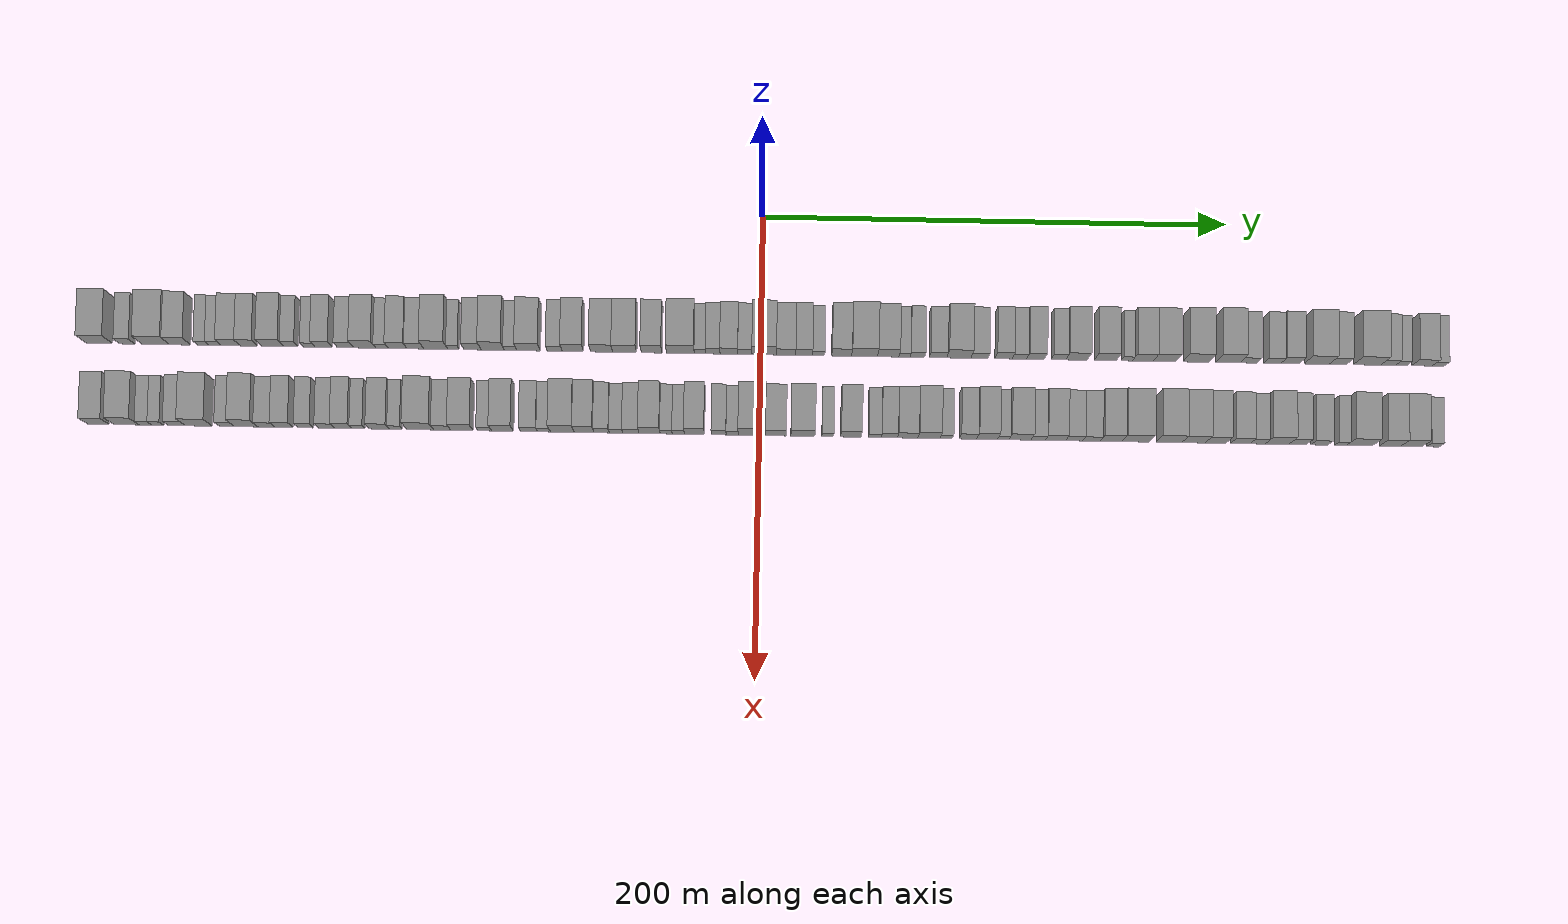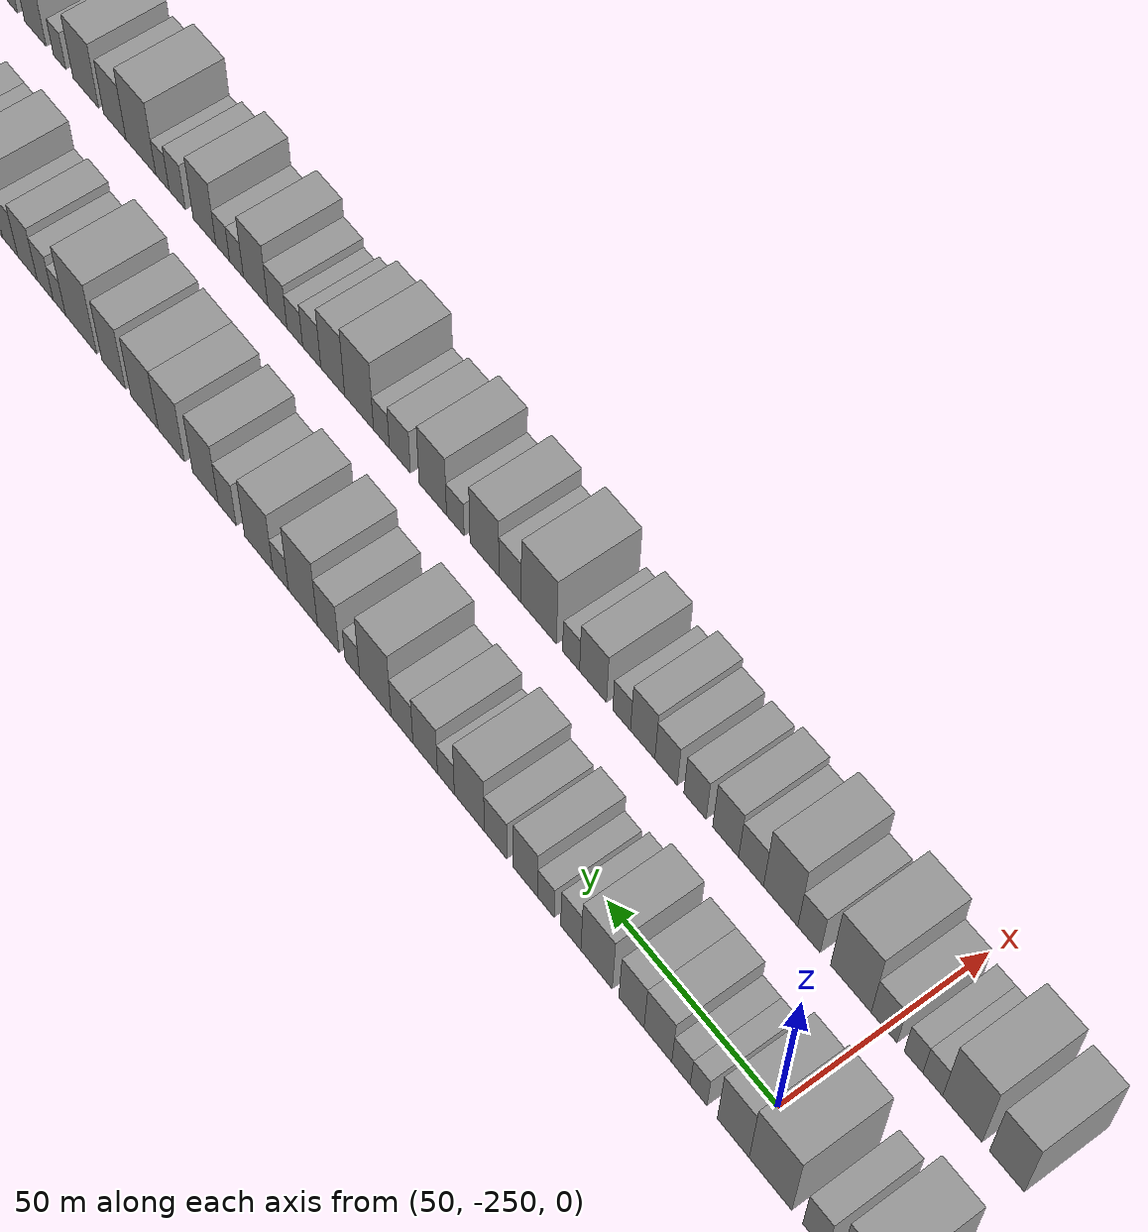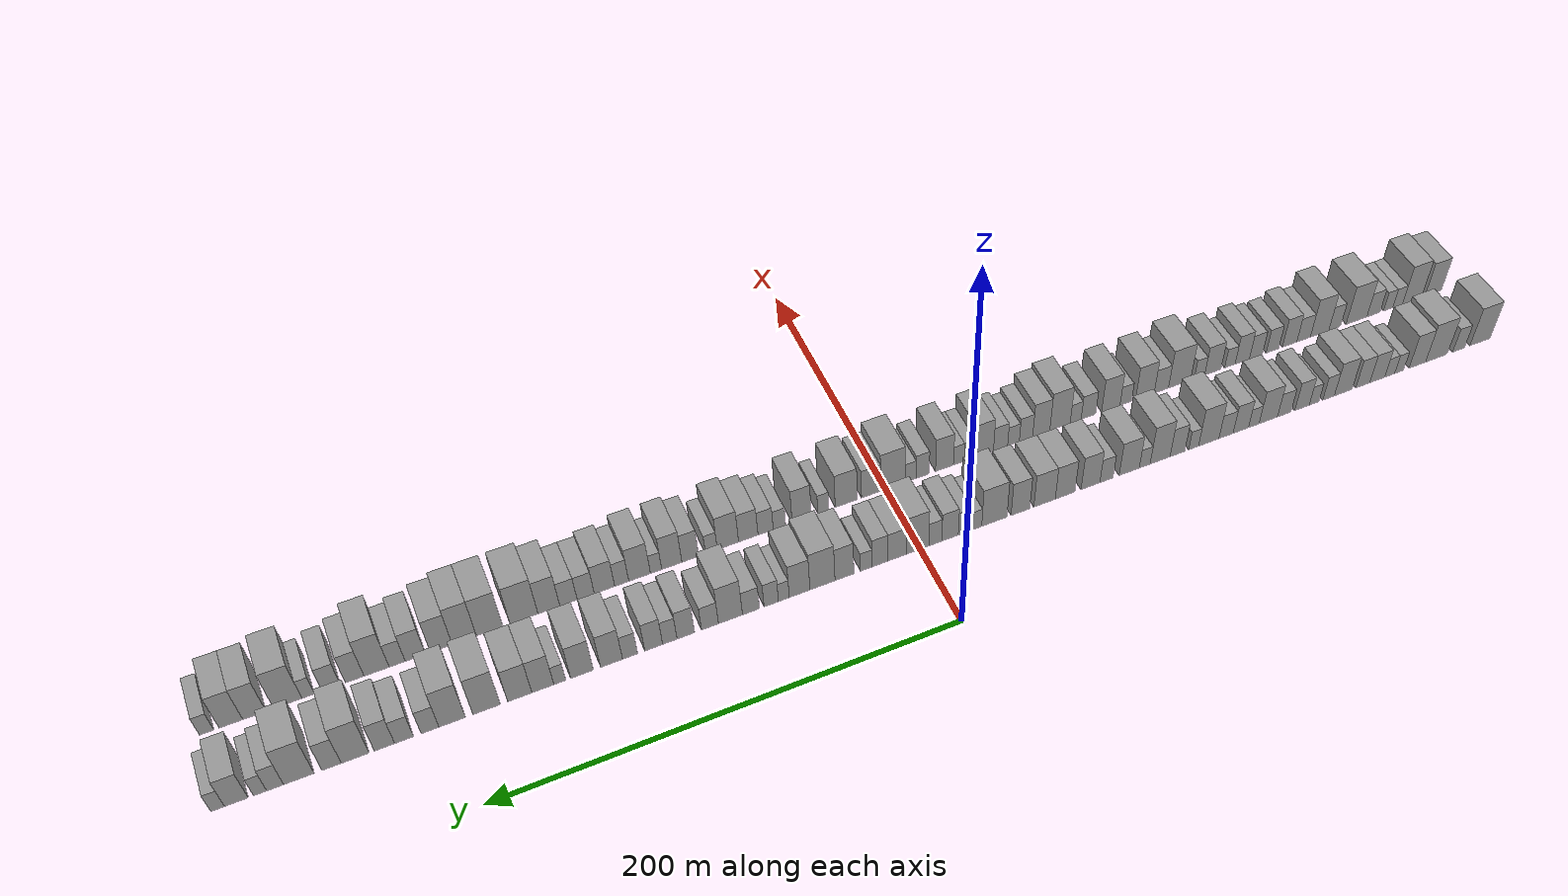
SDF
<sdf version="1.6">
 <world name="default">
  <scene>
   <sky><clouds><speed>12</speed></clouds></sky>
   <ambient>0.4 0.4 0.4 1</ambient>
   <background>0.7 0.7 0.7 1</background>
   <shadows>1</shadows>
  </scene>
  <gravity>0 0 -9.8066</gravity>
  <magnetic_field>6e-06 2.3e-05 -4.2e-05</magnetic_field>
  <physics default="0" name="default_physics" type="ode">
   <ode>
    <solver>
     <type>quick</type>
     <iters>10</iters>
     <sor>1.0</sor>
     <use_dynamic_moi_rescaling>0</use_dynamic_moi_rescaling>
    </solver>
    <constraints>
     <cfm>0</cfm>
     <erp>0.2</erp>
     <contact_max_correcting_vel>100</contact_max_correcting_vel>
     <contact_surface_layer>0.001</contact_surface_layer>
    </constraints>
   </ode>
   <max_step_size>0.004</max_step_size>
   <real_time_factor>1</real_time_factor>
   <real_time_update_rate>250</real_time_update_rate>
  </physics>
  <light name="sun" type="directional">
   <pose>0 0 10 0 0 0</pose>
   <diffuse>0.8 0.8 0.8 1</diffuse>
   <specular>0.2 0.2 0.2 1</specular>
   <attenuation>
    <range>1000</range>
    <constant>0.9</constant>
    <linear>0.01</linear>
    <quadratic>0.001</quadratic>
   </attenuation>
   <direction>-0.5 0.1 -0.9</direction>
  </light>
  <model name="building_1">
   <static>1</static>
   <pose>50.0000 -284.3592 0 0.000000 0.000000 0.000000</pose>
   <link name="link">
    <pose>0 0 12.00 0 0 0</pose>
    <collision name="collision"><geometry><box><size>20.0000 11.2816 24.0000</size></box></geometry></collision>
    <visual name="visual">
     <cast_shadows>0</cast_shadows>
     <geometry><box><size>20.0000 11.2816 24.0000</size></box></geometry>
     <material>
      <script>
       <uri>model://grey_wall/materials/scripts</uri>
       <uri>model://grey_wall/materials/textures</uri>
       <name>vrc/grey_wall</name>
      </script>
     </material>
    </visual>
   </link>
  </model>
  <model name="building_2">
   <static>1</static>
   <pose>50.0000 -272.4377 0 0.000000 0.000000 0.000000</pose>
   <link name="link">
    <pose>0 0 7.50 0 0 0</pose>
    <collision name="collision"><geometry><box><size>20.0000 6.5613 15.0000</size></box></geometry></collision>
    <visual name="visual">
     <cast_shadows>0</cast_shadows>
     <geometry><box><size>20.0000 6.5613 15.0000</size></box></geometry>
     <material>
      <script>
       <uri>model://grey_wall/materials/scripts</uri>
       <uri>model://grey_wall/materials/textures</uri>
       <name>vrc/grey_wall</name>
      </script>
     </material>
    </visual>
   </link>
  </model>
  <model name="building_3">
   <static>1</static>
   <pose>50.0000 -260.1841 0 0.000000 0.000000 0.000000</pose>
   <link name="link">
    <pose>0 0 12.00 0 0 0</pose>
    <collision name="collision"><geometry><box><size>20.0000 11.9459 24.0000</size></box></geometry></collision>
    <visual name="visual">
     <cast_shadows>0</cast_shadows>
     <geometry><box><size>20.0000 11.9459 24.0000</size></box></geometry>
     <material>
      <script>
       <uri>model://grey_wall/materials/scripts</uri>
       <uri>model://grey_wall/materials/textures</uri>
       <name>vrc/grey_wall</name>
      </script>
     </material>
    </visual>
   </link>
  </model>
  <model name="building_4">
   <static>1</static>
   <pose>50.0000 -249.6946 0 0.000000 0.000000 0.000000</pose>
   <link name="link">
    <pose>0 0 10.50 0 0 0</pose>
    <collision name="collision"><geometry><box><size>20.0000 9.0331 21.0000</size></box></geometry></collision>
    <visual name="visual">
     <cast_shadows>0</cast_shadows>
     <geometry><box><size>20.0000 9.0331 21.0000</size></box></geometry>
     <material>
      <script>
       <uri>model://grey_wall/materials/scripts</uri>
       <uri>model://grey_wall/materials/textures</uri>
       <name>vrc/grey_wall</name>
      </script>
     </material>
    </visual>
   </link>
  </model>
  <model name="building_5">
   <static>1</static>
   <pose>50.0000 -239.7531 0 0.000000 0.000000 0.000000</pose>
   <link name="link">
    <pose>0 0 6.00 0 0 0</pose>
    <collision name="collision"><geometry><box><size>20.0000 4.8501 12.0000</size></box></geometry></collision>
    <visual name="visual">
     <cast_shadows>0</cast_shadows>
     <geometry><box><size>20.0000 4.8501 12.0000</size></box></geometry>
     <material>
      <script>
       <uri>model://grey_wall/materials/scripts</uri>
       <uri>model://grey_wall/materials/textures</uri>
       <name>vrc/grey_wall</name>
      </script>
     </material>
    </visual>
   </link>
  </model>
  <model name="building_6">
   <static>1</static>
   <pose>50.0000 -234.6435 0 0.000000 0.000000 0.000000</pose>
   <link name="link">
    <pose>0 0 6.00 0 0 0</pose>
    <collision name="collision"><geometry><box><size>20.0000 5.3691 12.0000</size></box></geometry></collision>
    <visual name="visual">
     <cast_shadows>0</cast_shadows>
     <geometry><box><size>20.0000 5.3691 12.0000</size></box></geometry>
     <material>
      <script>
       <uri>model://grey_wall/materials/scripts</uri>
       <uri>model://grey_wall/materials/textures</uri>
       <name>vrc/grey_wall</name>
      </script>
     </material>
    </visual>
   </link>
  </model>
  <model name="building_7">
   <static>1</static>
   <pose>50.0000 -227.8935 0 0.000000 0.000000 0.000000</pose>
   <link name="link">
    <pose>0 0 9.00 0 0 0</pose>
    <collision name="collision"><geometry><box><size>20.0000 8.1309 18.0000</size></box></geometry></collision>
    <visual name="visual">
     <cast_shadows>0</cast_shadows>
     <geometry><box><size>20.0000 8.1309 18.0000</size></box></geometry>
     <material>
      <script>
       <uri>model://grey_wall/materials/scripts</uri>
       <uri>model://grey_wall/materials/textures</uri>
       <name>vrc/grey_wall</name>
      </script>
     </material>
    </visual>
   </link>
  </model>
  <model name="building_8">
   <static>1</static>
   <pose>50.0000 -220.1073 0 0.000000 0.000000 0.000000</pose>
   <link name="link">
    <pose>0 0 9.00 0 0 0</pose>
    <collision name="collision"><geometry><box><size>20.0000 7.4415 18.0000</size></box></geometry></collision>
    <visual name="visual">
     <cast_shadows>0</cast_shadows>
     <geometry><box><size>20.0000 7.4415 18.0000</size></box></geometry>
     <material>
      <script>
       <uri>model://grey_wall/materials/scripts</uri>
       <uri>model://grey_wall/materials/textures</uri>
       <name>vrc/grey_wall</name>
      </script>
     </material>
    </visual>
   </link>
  </model>
  <model name="building_9">
   <static>1</static>
   <pose>50.0000 -209.6560 0 0.000000 0.000000 0.000000</pose>
   <link name="link">
    <pose>0 0 10.50 0 0 0</pose>
    <collision name="collision"><geometry><box><size>20.0000 9.4611 21.0000</size></box></geometry></collision>
    <visual name="visual">
     <cast_shadows>0</cast_shadows>
     <geometry><box><size>20.0000 9.4611 21.0000</size></box></geometry>
     <material>
      <script>
       <uri>model://grey_wall/materials/scripts</uri>
       <uri>model://grey_wall/materials/textures</uri>
       <name>vrc/grey_wall</name>
      </script>
     </material>
    </visual>
   </link>
  </model>
  <model name="building_10">
   <static>1</static>
   <pose>50.0000 -201.8469 0 0.000000 0.000000 0.000000</pose>
   <link name="link">
    <pose>0 0 7.50 0 0 0</pose>
    <collision name="collision"><geometry><box><size>20.0000 6.1570 15.0000</size></box></geometry></collision>
    <visual name="visual">
     <cast_shadows>0</cast_shadows>
     <geometry><box><size>20.0000 6.1570 15.0000</size></box></geometry>
     <material>
      <script>
       <uri>model://grey_wall/materials/scripts</uri>
       <uri>model://grey_wall/materials/textures</uri>
       <name>vrc/grey_wall</name>
      </script>
     </material>
    </visual>
   </link>
  </model>
  <model name="building_11">
   <static>1</static>
   <pose>50.0000 -194.1964 0 0.000000 0.000000 0.000000</pose>
   <link name="link">
    <pose>0 0 6.00 0 0 0</pose>
    <collision name="collision"><geometry><box><size>20.0000 5.1440 12.0000</size></box></geometry></collision>
    <visual name="visual">
     <cast_shadows>0</cast_shadows>
     <geometry><box><size>20.0000 5.1440 12.0000</size></box></geometry>
     <material>
      <script>
       <uri>model://grey_wall/materials/scripts</uri>
       <uri>model://grey_wall/materials/textures</uri>
       <name>vrc/grey_wall</name>
      </script>
     </material>
    </visual>
   </link>
  </model>
  <model name="building_12">
   <static>1</static>
   <pose>50.0000 -187.8328 0 0.000000 0.000000 0.000000</pose>
   <link name="link">
    <pose>0 0 9.00 0 0 0</pose>
    <collision name="collision"><geometry><box><size>20.0000 7.5832 18.0000</size></box></geometry></collision>
    <visual name="visual">
     <cast_shadows>0</cast_shadows>
     <geometry><box><size>20.0000 7.5832 18.0000</size></box></geometry>
     <material>
      <script>
       <uri>model://grey_wall/materials/scripts</uri>
       <uri>model://grey_wall/materials/textures</uri>
       <name>vrc/grey_wall</name>
      </script>
     </material>
    </visual>
   </link>
  </model>
  <model name="building_13">
   <static>1</static>
   <pose>50.0000 -178.5126 0 0.000000 0.000000 0.000000</pose>
   <link name="link">
    <pose>0 0 7.50 0 0 0</pose>
    <collision name="collision"><geometry><box><size>20.0000 7.0572 15.0000</size></box></geometry></collision>
    <visual name="visual">
     <cast_shadows>0</cast_shadows>
     <geometry><box><size>20.0000 7.0572 15.0000</size></box></geometry>
     <material>
      <script>
       <uri>model://grey_wall/materials/scripts</uri>
       <uri>model://grey_wall/materials/textures</uri>
       <name>vrc/grey_wall</name>
      </script>
     </material>
    </visual>
   </link>
  </model>
  <model name="building_14">
   <static>1</static>
   <pose>50.0000 -170.2077 0 0.000000 0.000000 0.000000</pose>
   <link name="link">
    <pose>0 0 10.50 0 0 0</pose>
    <collision name="collision"><geometry><box><size>20.0000 9.5524 21.0000</size></box></geometry></collision>
    <visual name="visual">
     <cast_shadows>0</cast_shadows>
     <geometry><box><size>20.0000 9.5524 21.0000</size></box></geometry>
     <material>
      <script>
       <uri>model://grey_wall/materials/scripts</uri>
       <uri>model://grey_wall/materials/textures</uri>
       <name>vrc/grey_wall</name>
      </script>
     </material>
    </visual>
   </link>
  </model>
  <model name="building_15">
   <static>1</static>
   <pose>50.0000 -162.7156 0 0.000000 0.000000 0.000000</pose>
   <link name="link">
    <pose>0 0 6.00 0 0 0</pose>
    <collision name="collision"><geometry><box><size>20.0000 5.4319 12.0000</size></box></geometry></collision>
    <visual name="visual">
     <cast_shadows>0</cast_shadows>
     <geometry><box><size>20.0000 5.4319 12.0000</size></box></geometry>
     <material>
      <script>
       <uri>model://grey_wall/materials/scripts</uri>
       <uri>model://grey_wall/materials/textures</uri>
       <name>vrc/grey_wall</name>
      </script>
     </material>
    </visual>
   </link>
  </model>
  <model name="building_16">
   <static>1</static>
   <pose>50.0000 -156.0095 0 0.000000 0.000000 0.000000</pose>
   <link name="link">
    <pose>0 0 9.00 0 0 0</pose>
    <collision name="collision"><geometry><box><size>20.0000 7.9802 18.0000</size></box></geometry></collision>
    <visual name="visual">
     <cast_shadows>0</cast_shadows>
     <geometry><box><size>20.0000 7.9802 18.0000</size></box></geometry>
     <material>
      <script>
       <uri>model://grey_wall/materials/scripts</uri>
       <uri>model://grey_wall/materials/textures</uri>
       <name>vrc/grey_wall</name>
      </script>
     </material>
    </visual>
   </link>
  </model>
  <model name="building_17">
   <static>1</static>
   <pose>50.0000 -148.4073 0 0.000000 0.000000 0.000000</pose>
   <link name="link">
    <pose>0 0 7.50 0 0 0</pose>
    <collision name="collision"><geometry><box><size>20.0000 7.2241 15.0000</size></box></geometry></collision>
    <visual name="visual">
     <cast_shadows>0</cast_shadows>
     <geometry><box><size>20.0000 7.2241 15.0000</size></box></geometry>
     <material>
      <script>
       <uri>model://grey_wall/materials/scripts</uri>
       <uri>model://grey_wall/materials/textures</uri>
       <name>vrc/grey_wall</name>
      </script>
     </material>
    </visual>
   </link>
  </model>
  <model name="building_18">
   <static>1</static>
   <pose>50.0000 -139.5887 0 0.000000 0.000000 0.000000</pose>
   <link name="link">
    <pose>0 0 12.00 0 0 0</pose>
    <collision name="collision"><geometry><box><size>20.0000 10.4132 24.0000</size></box></geometry></collision>
    <visual name="visual">
     <cast_shadows>0</cast_shadows>
     <geometry><box><size>20.0000 10.4132 24.0000</size></box></geometry>
     <material>
      <script>
       <uri>model://grey_wall/materials/scripts</uri>
       <uri>model://grey_wall/materials/textures</uri>
       <name>vrc/grey_wall</name>
      </script>
     </material>
    </visual>
   </link>
  </model>
  <model name="building_19">
   <static>1</static>
   <pose>50.0000 -131.9105 0 0.000000 0.000000 0.000000</pose>
   <link name="link">
    <pose>0 0 6.00 0 0 0</pose>
    <collision name="collision"><geometry><box><size>20.0000 4.9431 12.0000</size></box></geometry></collision>
    <visual name="visual">
     <cast_shadows>0</cast_shadows>
     <geometry><box><size>20.0000 4.9431 12.0000</size></box></geometry>
     <material>
      <script>
       <uri>model://grey_wall/materials/scripts</uri>
       <uri>model://grey_wall/materials/textures</uri>
       <name>vrc/grey_wall</name>
      </script>
     </material>
    </visual>
   </link>
  </model>
  <model name="building_20">
   <static>1</static>
   <pose>50.0000 -123.7451 0 0.000000 0.000000 0.000000</pose>
   <link name="link">
    <pose>0 0 9.00 0 0 0</pose>
    <collision name="collision"><geometry><box><size>20.0000 7.3878 18.0000</size></box></geometry></collision>
    <visual name="visual">
     <cast_shadows>0</cast_shadows>
     <geometry><box><size>20.0000 7.3878 18.0000</size></box></geometry>
     <material>
      <script>
       <uri>model://grey_wall/materials/scripts</uri>
       <uri>model://grey_wall/materials/textures</uri>
       <name>vrc/grey_wall</name>
      </script>
     </material>
    </visual>
   </link>
  </model>
  <model name="building_21">
   <static>1</static>
   <pose>50.0000 -115.0648 0 0.000000 0.000000 0.000000</pose>
   <link name="link">
    <pose>0 0 12.00 0 0 0</pose>
    <collision name="collision"><geometry><box><size>20.0000 9.9729 24.0000</size></box></geometry></collision>
    <visual name="visual">
     <cast_shadows>0</cast_shadows>
     <geometry><box><size>20.0000 9.9729 24.0000</size></box></geometry>
     <material>
      <script>
       <uri>model://grey_wall/materials/scripts</uri>
       <uri>model://grey_wall/materials/textures</uri>
       <name>vrc/grey_wall</name>
      </script>
     </material>
    </visual>
   </link>
  </model>
  <model name="building_22">
   <static>1</static>
   <pose>50.0000 -107.3679 0 0.000000 0.000000 0.000000</pose>
   <link name="link">
    <pose>0 0 6.00 0 0 0</pose>
    <collision name="collision"><geometry><box><size>20.0000 5.4209 12.0000</size></box></geometry></collision>
    <visual name="visual">
     <cast_shadows>0</cast_shadows>
     <geometry><box><size>20.0000 5.4209 12.0000</size></box></geometry>
     <material>
      <script>
       <uri>model://grey_wall/materials/scripts</uri>
       <uri>model://grey_wall/materials/textures</uri>
       <name>vrc/grey_wall</name>
      </script>
     </material>
    </visual>
   </link>
  </model>
  <model name="building_23">
   <static>1</static>
   <pose>50.0000 -99.6649 0 0.000000 0.000000 0.000000</pose>
   <link name="link">
    <pose>0 0 10.50 0 0 0</pose>
    <collision name="collision"><geometry><box><size>20.0000 9.9850 21.0000</size></box></geometry></collision>
    <visual name="visual">
     <cast_shadows>0</cast_shadows>
     <geometry><box><size>20.0000 9.9850 21.0000</size></box></geometry>
     <material>
      <script>
       <uri>model://grey_wall/materials/scripts</uri>
       <uri>model://grey_wall/materials/textures</uri>
       <name>vrc/grey_wall</name>
      </script>
     </material>
    </visual>
   </link>
  </model>
  <model name="building_24">
   <static>1</static>
   <pose>50.0000 -88.4463 0 0.000000 0.000000 0.000000</pose>
   <link name="link">
    <pose>0 0 7.50 0 0 0</pose>
    <collision name="collision"><geometry><box><size>20.0000 6.4522 15.0000</size></box></geometry></collision>
    <visual name="visual">
     <cast_shadows>0</cast_shadows>
     <geometry><box><size>20.0000 6.4522 15.0000</size></box></geometry>
     <material>
      <script>
       <uri>model://grey_wall/materials/scripts</uri>
       <uri>model://grey_wall/materials/textures</uri>
       <name>vrc/grey_wall</name>
      </script>
     </material>
    </visual>
   </link>
  </model>
  <model name="building_25">
   <static>1</static>
   <pose>50.0000 -80.6226 0 0.000000 0.000000 0.000000</pose>
   <link name="link">
    <pose>0 0 10.50 0 0 0</pose>
    <collision name="collision"><geometry><box><size>20.0000 9.1952 21.0000</size></box></geometry></collision>
    <visual name="visual">
     <cast_shadows>0</cast_shadows>
     <geometry><box><size>20.0000 9.1952 21.0000</size></box></geometry>
     <material>
      <script>
       <uri>model://grey_wall/materials/scripts</uri>
       <uri>model://grey_wall/materials/textures</uri>
       <name>vrc/grey_wall</name>
      </script>
     </material>
    </visual>
   </link>
  </model>
  <model name="building_26">
   <static>1</static>
   <pose>50.0000 -68.2585 0 0.000000 0.000000 0.000000</pose>
   <link name="link">
    <pose>0 0 10.50 0 0 0</pose>
    <collision name="collision"><geometry><box><size>20.0000 9.5330 21.0000</size></box></geometry></collision>
    <visual name="visual">
     <cast_shadows>0</cast_shadows>
     <geometry><box><size>20.0000 9.5330 21.0000</size></box></geometry>
     <material>
      <script>
       <uri>model://grey_wall/materials/scripts</uri>
       <uri>model://grey_wall/materials/textures</uri>
       <name>vrc/grey_wall</name>
      </script>
     </material>
    </visual>
   </link>
  </model>
  <model name="building_27">
   <static>1</static>
   <pose>50.0000 -58.3447 0 0.000000 0.000000 0.000000</pose>
   <link name="link">
    <pose>0 0 10.50 0 0 0</pose>
    <collision name="collision"><geometry><box><size>20.0000 10.2946 21.0000</size></box></geometry></collision>
    <visual name="visual">
     <cast_shadows>0</cast_shadows>
     <geometry><box><size>20.0000 10.2946 21.0000</size></box></geometry>
     <material>
      <script>
       <uri>model://grey_wall/materials/scripts</uri>
       <uri>model://grey_wall/materials/textures</uri>
       <name>vrc/grey_wall</name>
      </script>
     </material>
    </visual>
   </link>
  </model>
  <model name="building_28">
   <static>1</static>
   <pose>50.0000 -46.7667 0 0.000000 0.000000 0.000000</pose>
   <link name="link">
    <pose>0 0 10.50 0 0 0</pose>
    <collision name="collision"><geometry><box><size>20.0000 8.8614 21.0000</size></box></geometry></collision>
    <visual name="visual">
     <cast_shadows>0</cast_shadows>
     <geometry><box><size>20.0000 8.8614 21.0000</size></box></geometry>
     <material>
      <script>
       <uri>model://grey_wall/materials/scripts</uri>
       <uri>model://grey_wall/materials/textures</uri>
       <name>vrc/grey_wall</name>
      </script>
     </material>
    </visual>
   </link>
  </model>
  <model name="building_29">
   <static>1</static>
   <pose>50.0000 -34.3768 0 0.000000 0.000000 0.000000</pose>
   <link name="link">
    <pose>0 0 12.00 0 0 0</pose>
    <collision name="collision"><geometry><box><size>20.0000 11.9185 24.0000</size></box></geometry></collision>
    <visual name="visual">
     <cast_shadows>0</cast_shadows>
     <geometry><box><size>20.0000 11.9185 24.0000</size></box></geometry>
     <material>
      <script>
       <uri>model://grey_wall/materials/scripts</uri>
       <uri>model://grey_wall/materials/textures</uri>
       <name>vrc/grey_wall</name>
      </script>
     </material>
    </visual>
   </link>
  </model>
  <model name="building_30">
   <static>1</static>
   <pose>50.0000 -26.0128 0 0.000000 0.000000 0.000000</pose>
   <link name="link">
    <pose>0 0 6.00 0 0 0</pose>
    <collision name="collision"><geometry><box><size>20.0000 4.8096 12.0000</size></box></geometry></collision>
    <visual name="visual">
     <cast_shadows>0</cast_shadows>
     <geometry><box><size>20.0000 4.8096 12.0000</size></box></geometry>
     <material>
      <script>
       <uri>model://grey_wall/materials/scripts</uri>
       <uri>model://grey_wall/materials/textures</uri>
       <name>vrc/grey_wall</name>
      </script>
     </material>
    </visual>
   </link>
  </model>
  <model name="building_31">
   <static>1</static>
   <pose>50.0000 -20.5107 0 0.000000 0.000000 0.000000</pose>
   <link name="link">
    <pose>0 0 7.50 0 0 0</pose>
    <collision name="collision"><geometry><box><size>20.0000 6.1945 15.0000</size></box></geometry></collision>
    <visual name="visual">
     <cast_shadows>0</cast_shadows>
     <geometry><box><size>20.0000 6.1945 15.0000</size></box></geometry>
     <material>
      <script>
       <uri>model://grey_wall/materials/scripts</uri>
       <uri>model://grey_wall/materials/textures</uri>
       <name>vrc/grey_wall</name>
      </script>
     </material>
    </visual>
   </link>
  </model>
  <model name="building_32">
   <static>1</static>
   <pose>50.0000 -13.5661 0 0.000000 0.000000 0.000000</pose>
   <link name="link">
    <pose>0 0 9.00 0 0 0</pose>
    <collision name="collision"><geometry><box><size>20.0000 7.6948 18.0000</size></box></geometry></collision>
    <visual name="visual">
     <cast_shadows>0</cast_shadows>
     <geometry><box><size>20.0000 7.6948 18.0000</size></box></geometry>
     <material>
      <script>
       <uri>model://grey_wall/materials/scripts</uri>
       <uri>model://grey_wall/materials/textures</uri>
       <name>vrc/grey_wall</name>
      </script>
     </material>
    </visual>
   </link>
  </model>
  <model name="building_33">
   <static>1</static>
   <pose>50.0000 -6.7014 0 0.000000 0.000000 0.000000</pose>
   <link name="link">
    <pose>0 0 7.50 0 0 0</pose>
    <collision name="collision"><geometry><box><size>20.0000 6.0345 15.0000</size></box></geometry></collision>
    <visual name="visual">
     <cast_shadows>0</cast_shadows>
     <geometry><box><size>20.0000 6.0345 15.0000</size></box></geometry>
     <material>
      <script>
       <uri>model://grey_wall/materials/scripts</uri>
       <uri>model://grey_wall/materials/textures</uri>
       <name>vrc/grey_wall</name>
      </script>
     </material>
    </visual>
   </link>
  </model>
  <model name="building_34">
   <static>1</static>
   <pose>50.0000 1.5610 0 0.000000 0.000000 0.000000</pose>
   <link name="link">
    <pose>0 0 12.00 0 0 0</pose>
    <collision name="collision"><geometry><box><size>20.0000 10.4904 24.0000</size></box></geometry></collision>
    <visual name="visual">
     <cast_shadows>0</cast_shadows>
     <geometry><box><size>20.0000 10.4904 24.0000</size></box></geometry>
     <material>
      <script>
       <uri>model://grey_wall/materials/scripts</uri>
       <uri>model://grey_wall/materials/textures</uri>
       <name>vrc/grey_wall</name>
      </script>
     </material>
    </visual>
   </link>
  </model>
  <model name="building_35">
   <static>1</static>
   <pose>50.0000 10.9428 0 0.000000 0.000000 0.000000</pose>
   <link name="link">
    <pose>0 0 9.00 0 0 0</pose>
    <collision name="collision"><geometry><box><size>20.0000 8.2730 18.0000</size></box></geometry></collision>
    <visual name="visual">
     <cast_shadows>0</cast_shadows>
     <geometry><box><size>20.0000 8.2730 18.0000</size></box></geometry>
     <material>
      <script>
       <uri>model://grey_wall/materials/scripts</uri>
       <uri>model://grey_wall/materials/textures</uri>
       <name>vrc/grey_wall</name>
      </script>
     </material>
    </visual>
   </link>
  </model>
  <model name="building_36">
   <static>1</static>
   <pose>50.0000 18.6821 0 0.000000 0.000000 0.000000</pose>
   <link name="link">
    <pose>0 0 9.00 0 0 0</pose>
    <collision name="collision"><geometry><box><size>20.0000 7.2055 18.0000</size></box></geometry></collision>
    <visual name="visual">
     <cast_shadows>0</cast_shadows>
     <geometry><box><size>20.0000 7.2055 18.0000</size></box></geometry>
     <material>
      <script>
       <uri>model://grey_wall/materials/scripts</uri>
       <uri>model://grey_wall/materials/textures</uri>
       <name>vrc/grey_wall</name>
      </script>
     </material>
    </visual>
   </link>
  </model>
  <model name="building_37">
   <static>1</static>
   <pose>50.0000 24.9326 0 0.000000 0.000000 0.000000</pose>
   <link name="link">
    <pose>0 0 6.00 0 0 0</pose>
    <collision name="collision"><geometry><box><size>20.0000 5.2955 12.0000</size></box></geometry></collision>
    <visual name="visual">
     <cast_shadows>0</cast_shadows>
     <geometry><box><size>20.0000 5.2955 12.0000</size></box></geometry>
     <material>
      <script>
       <uri>model://grey_wall/materials/scripts</uri>
       <uri>model://grey_wall/materials/textures</uri>
       <name>vrc/grey_wall</name>
      </script>
     </material>
    </visual>
   </link>
  </model>
  <model name="building_38">
   <static>1</static>
   <pose>50.0000 34.8326 0 0.000000 0.000000 0.000000</pose>
   <link name="link">
    <pose>0 0 10.50 0 0 0</pose>
    <collision name="collision"><geometry><box><size>20.0000 8.5047 21.0000</size></box></geometry></collision>
    <visual name="visual">
     <cast_shadows>0</cast_shadows>
     <geometry><box><size>20.0000 8.5047 21.0000</size></box></geometry>
     <material>
      <script>
       <uri>model://grey_wall/materials/scripts</uri>
       <uri>model://grey_wall/materials/textures</uri>
       <name>vrc/grey_wall</name>
      </script>
     </material>
    </visual>
   </link>
  </model>
  <model name="building_39">
   <static>1</static>
   <pose>50.0000 44.6915 0 0.000000 0.000000 0.000000</pose>
   <link name="link">
    <pose>0 0 12.00 0 0 0</pose>
    <collision name="collision"><geometry><box><size>20.0000 11.2131 24.0000</size></box></geometry></collision>
    <visual name="visual">
     <cast_shadows>0</cast_shadows>
     <geometry><box><size>20.0000 11.2131 24.0000</size></box></geometry>
     <material>
      <script>
       <uri>model://grey_wall/materials/scripts</uri>
       <uri>model://grey_wall/materials/textures</uri>
       <name>vrc/grey_wall</name>
      </script>
     </material>
    </visual>
   </link>
  </model>
  <model name="building_40">
   <static>1</static>
   <pose>50.0000 54.8790 0 0.000000 0.000000 0.000000</pose>
   <link name="link">
    <pose>0 0 10.50 0 0 0</pose>
    <collision name="collision"><geometry><box><size>20.0000 9.1619 21.0000</size></box></geometry></collision>
    <visual name="visual">
     <cast_shadows>0</cast_shadows>
     <geometry><box><size>20.0000 9.1619 21.0000</size></box></geometry>
     <material>
      <script>
       <uri>model://grey_wall/materials/scripts</uri>
       <uri>model://grey_wall/materials/textures</uri>
       <name>vrc/grey_wall</name>
      </script>
     </material>
    </visual>
   </link>
  </model>
  <model name="building_41">
   <static>1</static>
   <pose>50.0000 61.8659 0 0.000000 0.000000 0.000000</pose>
   <link name="link">
    <pose>0 0 6.00 0 0 0</pose>
    <collision name="collision"><geometry><box><size>20.0000 4.8118 12.0000</size></box></geometry></collision>
    <visual name="visual">
     <cast_shadows>0</cast_shadows>
     <geometry><box><size>20.0000 4.8118 12.0000</size></box></geometry>
     <material>
      <script>
       <uri>model://grey_wall/materials/scripts</uri>
       <uri>model://grey_wall/materials/textures</uri>
       <name>vrc/grey_wall</name>
      </script>
     </material>
    </visual>
   </link>
  </model>
  <model name="building_42">
   <static>1</static>
   <pose>50.0000 67.4363 0 0.000000 0.000000 0.000000</pose>
   <link name="link">
    <pose>0 0 7.50 0 0 0</pose>
    <collision name="collision"><geometry><box><size>20.0000 6.3291 15.0000</size></box></geometry></collision>
    <visual name="visual">
     <cast_shadows>0</cast_shadows>
     <geometry><box><size>20.0000 6.3291 15.0000</size></box></geometry>
     <material>
      <script>
       <uri>model://grey_wall/materials/scripts</uri>
       <uri>model://grey_wall/materials/textures</uri>
       <name>vrc/grey_wall</name>
      </script>
     </material>
    </visual>
   </link>
  </model>
  <model name="building_43">
   <static>1</static>
   <pose>50.0000 76.3273 0 0.000000 0.000000 0.000000</pose>
   <link name="link">
    <pose>0 0 7.50 0 0 0</pose>
    <collision name="collision"><geometry><box><size>20.0000 7.4528 15.0000</size></box></geometry></collision>
    <visual name="visual">
     <cast_shadows>0</cast_shadows>
     <geometry><box><size>20.0000 7.4528 15.0000</size></box></geometry>
     <material>
      <script>
       <uri>model://grey_wall/materials/scripts</uri>
       <uri>model://grey_wall/materials/textures</uri>
       <name>vrc/grey_wall</name>
      </script>
     </material>
    </visual>
   </link>
  </model>
  <model name="building_44">
   <static>1</static>
   <pose>50.0000 85.2699 0 0.000000 0.000000 0.000000</pose>
   <link name="link">
    <pose>0 0 12.00 0 0 0</pose>
    <collision name="collision"><geometry><box><size>20.0000 10.4325 24.0000</size></box></geometry></collision>
    <visual name="visual">
     <cast_shadows>0</cast_shadows>
     <geometry><box><size>20.0000 10.4325 24.0000</size></box></geometry>
     <material>
      <script>
       <uri>model://grey_wall/materials/scripts</uri>
       <uri>model://grey_wall/materials/textures</uri>
       <name>vrc/grey_wall</name>
      </script>
     </material>
    </visual>
   </link>
  </model>
  <model name="building_45">
   <static>1</static>
   <pose>50.0000 94.1355 0 0.000000 0.000000 0.000000</pose>
   <link name="link">
    <pose>0 0 7.50 0 0 0</pose>
    <collision name="collision"><geometry><box><size>20.0000 7.2986 15.0000</size></box></geometry></collision>
    <visual name="visual">
     <cast_shadows>0</cast_shadows>
     <geometry><box><size>20.0000 7.2986 15.0000</size></box></geometry>
     <material>
      <script>
       <uri>model://grey_wall/materials/scripts</uri>
       <uri>model://grey_wall/materials/textures</uri>
       <name>vrc/grey_wall</name>
      </script>
     </material>
    </visual>
   </link>
  </model>
  <model name="building_46">
   <static>1</static>
   <pose>50.0000 104.5383 0 0.000000 0.000000 0.000000</pose>
   <link name="link">
    <pose>0 0 9.00 0 0 0</pose>
    <collision name="collision"><geometry><box><size>20.0000 7.5070 18.0000</size></box></geometry></collision>
    <visual name="visual">
     <cast_shadows>0</cast_shadows>
     <geometry><box><size>20.0000 7.5070 18.0000</size></box></geometry>
     <material>
      <script>
       <uri>model://grey_wall/materials/scripts</uri>
       <uri>model://grey_wall/materials/textures</uri>
       <name>vrc/grey_wall</name>
      </script>
     </material>
    </visual>
   </link>
  </model>
  <model name="building_47">
   <static>1</static>
   <pose>50.0000 111.3633 0 0.000000 0.000000 0.000000</pose>
   <link name="link">
    <pose>0 0 7.50 0 0 0</pose>
    <collision name="collision"><geometry><box><size>20.0000 6.1431 15.0000</size></box></geometry></collision>
    <visual name="visual">
     <cast_shadows>0</cast_shadows>
     <geometry><box><size>20.0000 6.1431 15.0000</size></box></geometry>
     <material>
      <script>
       <uri>model://grey_wall/materials/scripts</uri>
       <uri>model://grey_wall/materials/textures</uri>
       <name>vrc/grey_wall</name>
      </script>
     </material>
    </visual>
   </link>
  </model>
  <model name="building_48">
   <static>1</static>
   <pose>50.0000 118.2187 0 0.000000 0.000000 0.000000</pose>
   <link name="link">
    <pose>0 0 9.00 0 0 0</pose>
    <collision name="collision"><geometry><box><size>20.0000 7.5677 18.0000</size></box></geometry></collision>
    <visual name="visual">
     <cast_shadows>0</cast_shadows>
     <geometry><box><size>20.0000 7.5677 18.0000</size></box></geometry>
     <material>
      <script>
       <uri>model://grey_wall/materials/scripts</uri>
       <uri>model://grey_wall/materials/textures</uri>
       <name>vrc/grey_wall</name>
      </script>
     </material>
    </visual>
   </link>
  </model>
  <model name="building_49">
   <static>1</static>
   <pose>50.0000 128.1905 0 0.000000 0.000000 0.000000</pose>
   <link name="link">
    <pose>0 0 7.50 0 0 0</pose>
    <collision name="collision"><geometry><box><size>20.0000 6.3759 15.0000</size></box></geometry></collision>
    <visual name="visual">
     <cast_shadows>0</cast_shadows>
     <geometry><box><size>20.0000 6.3759 15.0000</size></box></geometry>
     <material>
      <script>
       <uri>model://grey_wall/materials/scripts</uri>
       <uri>model://grey_wall/materials/textures</uri>
       <name>vrc/grey_wall</name>
      </script>
     </material>
    </visual>
   </link>
  </model>
  <model name="building_50">
   <static>1</static>
   <pose>50.0000 135.9587 0 0.000000 0.000000 0.000000</pose>
   <link name="link">
    <pose>0 0 10.50 0 0 0</pose>
    <collision name="collision"><geometry><box><size>20.0000 9.1605 21.0000</size></box></geometry></collision>
    <visual name="visual">
     <cast_shadows>0</cast_shadows>
     <geometry><box><size>20.0000 9.1605 21.0000</size></box></geometry>
     <material>
      <script>
       <uri>model://grey_wall/materials/scripts</uri>
       <uri>model://grey_wall/materials/textures</uri>
       <name>vrc/grey_wall</name>
      </script>
     </material>
    </visual>
   </link>
  </model>
  <model name="building_51">
   <static>1</static>
   <pose>50.0000 148.2885 0 0.000000 0.000000 0.000000</pose>
   <link name="link">
    <pose>0 0 10.50 0 0 0</pose>
    <collision name="collision"><geometry><box><size>20.0000 9.4992 21.0000</size></box></geometry></collision>
    <visual name="visual">
     <cast_shadows>0</cast_shadows>
     <geometry><box><size>20.0000 9.4992 21.0000</size></box></geometry>
     <material>
      <script>
       <uri>model://grey_wall/materials/scripts</uri>
       <uri>model://grey_wall/materials/textures</uri>
       <name>vrc/grey_wall</name>
      </script>
     </material>
    </visual>
   </link>
  </model>
  <model name="building_52">
   <static>1</static>
   <pose>50.0000 157.4965 0 0.000000 0.000000 0.000000</pose>
   <link name="link">
    <pose>0 0 6.00 0 0 0</pose>
    <collision name="collision"><geometry><box><size>20.0000 4.9168 12.0000</size></box></geometry></collision>
    <visual name="visual">
     <cast_shadows>0</cast_shadows>
     <geometry><box><size>20.0000 4.9168 12.0000</size></box></geometry>
     <material>
      <script>
       <uri>model://grey_wall/materials/scripts</uri>
       <uri>model://grey_wall/materials/textures</uri>
       <name>vrc/grey_wall</name>
      </script>
     </material>
    </visual>
   </link>
  </model>
  <model name="building_53">
   <static>1</static>
   <pose>50.0000 164.4559 0 0.000000 0.000000 0.000000</pose>
   <link name="link">
    <pose>0 0 10.50 0 0 0</pose>
    <collision name="collision"><geometry><box><size>20.0000 9.0020 21.0000</size></box></geometry></collision>
    <visual name="visual">
     <cast_shadows>0</cast_shadows>
     <geometry><box><size>20.0000 9.0020 21.0000</size></box></geometry>
     <material>
      <script>
       <uri>model://grey_wall/materials/scripts</uri>
       <uri>model://grey_wall/materials/textures</uri>
       <name>vrc/grey_wall</name>
      </script>
     </material>
    </visual>
   </link>
  </model>
  <model name="building_54">
   <static>1</static>
   <pose>50.0000 173.8521 0 0.000000 0.000000 0.000000</pose>
   <link name="link">
    <pose>0 0 10.50 0 0 0</pose>
    <collision name="collision"><geometry><box><size>20.0000 9.7904 21.0000</size></box></geometry></collision>
    <visual name="visual">
     <cast_shadows>0</cast_shadows>
     <geometry><box><size>20.0000 9.7904 21.0000</size></box></geometry>
     <material>
      <script>
       <uri>model://grey_wall/materials/scripts</uri>
       <uri>model://grey_wall/materials/textures</uri>
       <name>vrc/grey_wall</name>
      </script>
     </material>
    </visual>
   </link>
  </model>
  <model name="building_55">
   <static>1</static>
   <pose>50.0000 187.2806 0 0.000000 0.000000 0.000000</pose>
   <link name="link">
    <pose>0 0 12.00 0 0 0</pose>
    <collision name="collision"><geometry><box><size>20.0000 11.0665 24.0000</size></box></geometry></collision>
    <visual name="visual">
     <cast_shadows>0</cast_shadows>
     <geometry><box><size>20.0000 11.0665 24.0000</size></box></geometry>
     <material>
      <script>
       <uri>model://grey_wall/materials/scripts</uri>
       <uri>model://grey_wall/materials/textures</uri>
       <name>vrc/grey_wall</name>
      </script>
     </material>
    </visual>
   </link>
  </model>
  <model name="building_56">
   <static>1</static>
   <pose>50.0000 201.0953 0 0.000000 0.000000 0.000000</pose>
   <link name="link">
    <pose>0 0 12.00 0 0 0</pose>
    <collision name="collision"><geometry><box><size>20.0000 10.5628 24.0000</size></box></geometry></collision>
    <visual name="visual">
     <cast_shadows>0</cast_shadows>
     <geometry><box><size>20.0000 10.5628 24.0000</size></box></geometry>
     <material>
      <script>
       <uri>model://grey_wall/materials/scripts</uri>
       <uri>model://grey_wall/materials/textures</uri>
       <name>vrc/grey_wall</name>
      </script>
     </material>
    </visual>
   </link>
  </model>
  <model name="building_57">
   <static>1</static>
   <pose>50.0000 209.8972 0 0.000000 0.000000 0.000000</pose>
   <link name="link">
    <pose>0 0 7.50 0 0 0</pose>
    <collision name="collision"><geometry><box><size>20.0000 7.0411 15.0000</size></box></geometry></collision>
    <visual name="visual">
     <cast_shadows>0</cast_shadows>
     <geometry><box><size>20.0000 7.0411 15.0000</size></box></geometry>
     <material>
      <script>
       <uri>model://grey_wall/materials/scripts</uri>
       <uri>model://grey_wall/materials/textures</uri>
       <name>vrc/grey_wall</name>
      </script>
     </material>
    </visual>
   </link>
  </model>
  <model name="building_58">
   <static>1</static>
   <pose>50.0000 220.1323 0 0.000000 0.000000 0.000000</pose>
   <link name="link">
    <pose>0 0 7.50 0 0 0</pose>
    <collision name="collision"><geometry><box><size>20.0000 7.4291 15.0000</size></box></geometry></collision>
    <visual name="visual">
     <cast_shadows>0</cast_shadows>
     <geometry><box><size>20.0000 7.4291 15.0000</size></box></geometry>
     <material>
      <script>
       <uri>model://grey_wall/materials/scripts</uri>
       <uri>model://grey_wall/materials/textures</uri>
       <name>vrc/grey_wall</name>
      </script>
     </material>
    </visual>
   </link>
  </model>
  <model name="building_59">
   <static>1</static>
   <pose>50.0000 227.8187 0 0.000000 0.000000 0.000000</pose>
   <link name="link">
    <pose>0 0 9.00 0 0 0</pose>
    <collision name="collision"><geometry><box><size>20.0000 7.9437 18.0000</size></box></geometry></collision>
    <visual name="visual">
     <cast_shadows>0</cast_shadows>
     <geometry><box><size>20.0000 7.9437 18.0000</size></box></geometry>
     <material>
      <script>
       <uri>model://grey_wall/materials/scripts</uri>
       <uri>model://grey_wall/materials/textures</uri>
       <name>vrc/grey_wall</name>
      </script>
     </material>
    </visual>
   </link>
  </model>
  <model name="building_60">
   <static>1</static>
   <pose>50.0000 239.2063 0 0.000000 0.000000 0.000000</pose>
   <link name="link">
    <pose>0 0 12.00 0 0 0</pose>
    <collision name="collision"><geometry><box><size>20.0000 10.8313 24.0000</size></box></geometry></collision>
    <visual name="visual">
     <cast_shadows>0</cast_shadows>
     <geometry><box><size>20.0000 10.8313 24.0000</size></box></geometry>
     <material>
      <script>
       <uri>model://grey_wall/materials/scripts</uri>
       <uri>model://grey_wall/materials/textures</uri>
       <name>vrc/grey_wall</name>
      </script>
     </material>
    </visual>
   </link>
  </model>
  <model name="building_61">
   <static>1</static>
   <pose>50.0000 248.3287 0 0.000000 0.000000 0.000000</pose>
   <link name="link">
    <pose>0 0 9.00 0 0 0</pose>
    <collision name="collision"><geometry><box><size>20.0000 7.4135 18.0000</size></box></geometry></collision>
    <visual name="visual">
     <cast_shadows>0</cast_shadows>
     <geometry><box><size>20.0000 7.4135 18.0000</size></box></geometry>
     <material>
      <script>
       <uri>model://grey_wall/materials/scripts</uri>
       <uri>model://grey_wall/materials/textures</uri>
       <name>vrc/grey_wall</name>
      </script>
     </material>
    </visual>
   </link>
  </model>
  <model name="building_62">
   <static>1</static>
   <pose>50.0000 260.8437 0 0.000000 0.000000 0.000000</pose>
   <link name="link">
    <pose>0 0 12.00 0 0 0</pose>
    <collision name="collision"><geometry><box><size>20.0000 11.6165 24.0000</size></box></geometry></collision>
    <visual name="visual">
     <cast_shadows>0</cast_shadows>
     <geometry><box><size>20.0000 11.6165 24.0000</size></box></geometry>
     <material>
      <script>
       <uri>model://grey_wall/materials/scripts</uri>
       <uri>model://grey_wall/materials/textures</uri>
       <name>vrc/grey_wall</name>
      </script>
     </material>
    </visual>
   </link>
  </model>
  <model name="building_63">
   <static>1</static>
   <pose>50.0000 269.8460 0 0.000000 0.000000 0.000000</pose>
   <link name="link">
    <pose>0 0 7.50 0 0 0</pose>
    <collision name="collision"><geometry><box><size>20.0000 6.3880 15.0000</size></box></geometry></collision>
    <visual name="visual">
     <cast_shadows>0</cast_shadows>
     <geometry><box><size>20.0000 6.3880 15.0000</size></box></geometry>
     <material>
      <script>
       <uri>model://grey_wall/materials/scripts</uri>
       <uri>model://grey_wall/materials/textures</uri>
       <name>vrc/grey_wall</name>
      </script>
     </material>
    </visual>
   </link>
  </model>
  <model name="building_64">
   <static>1</static>
   <pose>50.0000 275.5295 0 0.000000 0.000000 0.000000</pose>
   <link name="link">
    <pose>0 0 6.00 0 0 0</pose>
    <collision name="collision"><geometry><box><size>20.0000 4.9792 12.0000</size></box></geometry></collision>
    <visual name="visual">
     <cast_shadows>0</cast_shadows>
     <geometry><box><size>20.0000 4.9792 12.0000</size></box></geometry>
     <material>
      <script>
       <uri>model://grey_wall/materials/scripts</uri>
       <uri>model://grey_wall/materials/textures</uri>
       <name>vrc/grey_wall</name>
      </script>
     </material>
    </visual>
   </link>
  </model>
  <model name="building_65">
   <static>1</static>
   <pose>50.0000 284.4295 0 0.000000 0.000000 0.000000</pose>
   <link name="link">
    <pose>0 0 9.00 0 0 0</pose>
    <collision name="collision"><geometry><box><size>20.0000 8.8207 18.0000</size></box></geometry></collision>
    <visual name="visual">
     <cast_shadows>0</cast_shadows>
     <geometry><box><size>20.0000 8.8207 18.0000</size></box></geometry>
     <material>
      <script>
       <uri>model://grey_wall/materials/scripts</uri>
       <uri>model://grey_wall/materials/textures</uri>
       <name>vrc/grey_wall</name>
      </script>
     </material>
    </visual>
   </link>
  </model>
  <model name="building_66">
   <static>1</static>
   <pose>50.0000 291.3864 0 0.000000 0.000000 0.000000</pose>
   <link name="link">
    <pose>0 0 6.00 0 0 0</pose>
    <collision name="collision"><geometry><box><size>20.0000 5.0931 12.0000</size></box></geometry></collision>
    <visual name="visual">
     <cast_shadows>0</cast_shadows>
     <geometry><box><size>20.0000 5.0931 12.0000</size></box></geometry>
     <material>
      <script>
       <uri>model://grey_wall/materials/scripts</uri>
       <uri>model://grey_wall/materials/textures</uri>
       <name>vrc/grey_wall</name>
      </script>
     </material>
    </visual>
   </link>
  </model>
  <model name="building_67">
   <static>1</static>
   <pose>85.0000 -283.3280 0 0.000000 0.000000 0.000000</pose>
   <link name="link">
    <pose>0 0 10.50 0 0 0</pose>
    <collision name="collision"><geometry><box><size>20.0000 9.3441 21.0000</size></box></geometry></collision>
    <visual name="visual">
     <cast_shadows>0</cast_shadows>
     <geometry><box><size>20.0000 9.3441 21.0000</size></box></geometry>
     <material>
      <script>
       <uri>model://grey_wall/materials/scripts</uri>
       <uri>model://grey_wall/materials/textures</uri>
       <name>vrc/grey_wall</name>
      </script>
     </material>
    </visual>
   </link>
  </model>
  <model name="building_68">
   <static>1</static>
   <pose>85.0000 -271.2954 0 0.000000 0.000000 0.000000</pose>
   <link name="link">
    <pose>0 0 12.00 0 0 0</pose>
    <collision name="collision"><geometry><box><size>20.0000 10.7210 24.0000</size></box></geometry></collision>
    <visual name="visual">
     <cast_shadows>0</cast_shadows>
     <geometry><box><size>20.0000 10.7210 24.0000</size></box></geometry>
     <material>
      <script>
       <uri>model://grey_wall/materials/scripts</uri>
       <uri>model://grey_wall/materials/textures</uri>
       <name>vrc/grey_wall</name>
      </script>
     </material>
    </visual>
   </link>
  </model>
  <model name="building_69">
   <static>1</static>
   <pose>85.0000 -263.2185 0 0.000000 0.000000 0.000000</pose>
   <link name="link">
    <pose>0 0 6.00 0 0 0</pose>
    <collision name="collision"><geometry><box><size>20.0000 5.4327 12.0000</size></box></geometry></collision>
    <visual name="visual">
     <cast_shadows>0</cast_shadows>
     <geometry><box><size>20.0000 5.4327 12.0000</size></box></geometry>
     <material>
      <script>
       <uri>model://grey_wall/materials/scripts</uri>
       <uri>model://grey_wall/materials/textures</uri>
       <name>vrc/grey_wall</name>
      </script>
     </material>
    </visual>
   </link>
  </model>
  <model name="building_70">
   <static>1</static>
   <pose>85.0000 -257.9267 0 0.000000 0.000000 0.000000</pose>
   <link name="link">
    <pose>0 0 6.00 0 0 0</pose>
    <collision name="collision"><geometry><box><size>20.0000 5.1511 12.0000</size></box></geometry></collision>
    <visual name="visual">
     <cast_shadows>0</cast_shadows>
     <geometry><box><size>20.0000 5.1511 12.0000</size></box></geometry>
     <material>
      <script>
       <uri>model://grey_wall/materials/scripts</uri>
       <uri>model://grey_wall/materials/textures</uri>
       <name>vrc/grey_wall</name>
      </script>
     </material>
    </visual>
   </link>
  </model>
  <model name="building_71">
   <static>1</static>
   <pose>85.0000 -249.7051 0 0.000000 0.000000 0.000000</pose>
   <link name="link">
    <pose>0 0 7.50 0 0 0</pose>
    <collision name="collision"><geometry><box><size>20.0000 7.2920 15.0000</size></box></geometry></collision>
    <visual name="visual">
     <cast_shadows>0</cast_shadows>
     <geometry><box><size>20.0000 7.2920 15.0000</size></box></geometry>
     <material>
      <script>
       <uri>model://grey_wall/materials/scripts</uri>
       <uri>model://grey_wall/materials/textures</uri>
       <name>vrc/grey_wall</name>
      </script>
     </material>
    </visual>
   </link>
  </model>
  <model name="building_72">
   <static>1</static>
   <pose>85.0000 -240.2894 0 0.000000 0.000000 0.000000</pose>
   <link name="link">
    <pose>0 0 12.00 0 0 0</pose>
    <collision name="collision"><geometry><box><size>20.0000 11.5393 24.0000</size></box></geometry></collision>
    <visual name="visual">
     <cast_shadows>0</cast_shadows>
     <geometry><box><size>20.0000 11.5393 24.0000</size></box></geometry>
     <material>
      <script>
       <uri>model://grey_wall/materials/scripts</uri>
       <uri>model://grey_wall/materials/textures</uri>
       <name>vrc/grey_wall</name>
      </script>
     </material>
    </visual>
   </link>
  </model>
  <model name="building_73">
   <static>1</static>
   <pose>85.0000 -228.2674 0 0.000000 0.000000 0.000000</pose>
   <link name="link">
    <pose>0 0 7.50 0 0 0</pose>
    <collision name="collision"><geometry><box><size>20.0000 6.5048 15.0000</size></box></geometry></collision>
    <visual name="visual">
     <cast_shadows>0</cast_shadows>
     <geometry><box><size>20.0000 6.5048 15.0000</size></box></geometry>
     <material>
      <script>
       <uri>model://grey_wall/materials/scripts</uri>
       <uri>model://grey_wall/materials/textures</uri>
       <name>vrc/grey_wall</name>
      </script>
     </material>
    </visual>
   </link>
  </model>
  <model name="building_74">
   <static>1</static>
   <pose>85.0000 -219.9922 0 0.000000 0.000000 0.000000</pose>
   <link name="link">
    <pose>0 0 12.00 0 0 0</pose>
    <collision name="collision"><geometry><box><size>20.0000 10.0457 24.0000</size></box></geometry></collision>
    <visual name="visual">
     <cast_shadows>0</cast_shadows>
     <geometry><box><size>20.0000 10.0457 24.0000</size></box></geometry>
     <material>
      <script>
       <uri>model://grey_wall/materials/scripts</uri>
       <uri>model://grey_wall/materials/textures</uri>
       <name>vrc/grey_wall</name>
      </script>
     </material>
    </visual>
   </link>
  </model>
  <model name="building_75">
   <static>1</static>
   <pose>85.0000 -211.2774 0 0.000000 0.000000 0.000000</pose>
   <link name="link">
    <pose>0 0 7.50 0 0 0</pose>
    <collision name="collision"><geometry><box><size>20.0000 7.3838 15.0000</size></box></geometry></collision>
    <visual name="visual">
     <cast_shadows>0</cast_shadows>
     <geometry><box><size>20.0000 7.3838 15.0000</size></box></geometry>
     <material>
      <script>
       <uri>model://grey_wall/materials/scripts</uri>
       <uri>model://grey_wall/materials/textures</uri>
       <name>vrc/grey_wall</name>
      </script>
     </material>
    </visual>
   </link>
  </model>
  <model name="building_76">
   <static>1</static>
   <pose>85.0000 -203.6915 0 0.000000 0.000000 0.000000</pose>
   <link name="link">
    <pose>0 0 9.00 0 0 0</pose>
    <collision name="collision"><geometry><box><size>20.0000 7.7880 18.0000</size></box></geometry></collision>
    <visual name="visual">
     <cast_shadows>0</cast_shadows>
     <geometry><box><size>20.0000 7.7880 18.0000</size></box></geometry>
     <material>
      <script>
       <uri>model://grey_wall/materials/scripts</uri>
       <uri>model://grey_wall/materials/textures</uri>
       <name>vrc/grey_wall</name>
      </script>
     </material>
    </visual>
   </link>
  </model>
  <model name="building_77">
   <static>1</static>
   <pose>85.0000 -194.4178 0 0.000000 0.000000 0.000000</pose>
   <link name="link">
    <pose>0 0 7.50 0 0 0</pose>
    <collision name="collision"><geometry><box><size>20.0000 6.7595 15.0000</size></box></geometry></collision>
    <visual name="visual">
     <cast_shadows>0</cast_shadows>
     <geometry><box><size>20.0000 6.7595 15.0000</size></box></geometry>
     <material>
      <script>
       <uri>model://grey_wall/materials/scripts</uri>
       <uri>model://grey_wall/materials/textures</uri>
       <name>vrc/grey_wall</name>
      </script>
     </material>
    </visual>
   </link>
  </model>
  <model name="building_78">
   <static>1</static>
   <pose>85.0000 -185.5821 0 0.000000 0.000000 0.000000</pose>
   <link name="link">
    <pose>0 0 7.50 0 0 0</pose>
    <collision name="collision"><geometry><box><size>20.0000 6.9118 15.0000</size></box></geometry></collision>
    <visual name="visual">
     <cast_shadows>0</cast_shadows>
     <geometry><box><size>20.0000 6.9118 15.0000</size></box></geometry>
     <material>
      <script>
       <uri>model://grey_wall/materials/scripts</uri>
       <uri>model://grey_wall/materials/textures</uri>
       <name>vrc/grey_wall</name>
      </script>
     </material>
    </visual>
   </link>
  </model>
  <model name="building_79">
   <static>1</static>
   <pose>85.0000 -178.3327 0 0.000000 0.000000 0.000000</pose>
   <link name="link">
    <pose>0 0 9.00 0 0 0</pose>
    <collision name="collision"><geometry><box><size>20.0000 7.5872 18.0000</size></box></geometry></collision>
    <visual name="visual">
     <cast_shadows>0</cast_shadows>
     <geometry><box><size>20.0000 7.5872 18.0000</size></box></geometry>
     <material>
      <script>
       <uri>model://grey_wall/materials/scripts</uri>
       <uri>model://grey_wall/materials/textures</uri>
       <name>vrc/grey_wall</name>
      </script>
     </material>
    </visual>
   </link>
  </model>
  <model name="building_80">
   <static>1</static>
   <pose>85.0000 -171.7712 0 0.000000 0.000000 0.000000</pose>
   <link name="link">
    <pose>0 0 6.00 0 0 0</pose>
    <collision name="collision"><geometry><box><size>20.0000 5.5357 12.0000</size></box></geometry></collision>
    <visual name="visual">
     <cast_shadows>0</cast_shadows>
     <geometry><box><size>20.0000 5.5357 12.0000</size></box></geometry>
     <material>
      <script>
       <uri>model://grey_wall/materials/scripts</uri>
       <uri>model://grey_wall/materials/textures</uri>
       <name>vrc/grey_wall</name>
      </script>
     </material>
    </visual>
   </link>
  </model>
  <model name="building_81">
   <static>1</static>
   <pose>85.0000 -162.7266 0 0.000000 0.000000 0.000000</pose>
   <link name="link">
    <pose>0 0 9.00 0 0 0</pose>
    <collision name="collision"><geometry><box><size>20.0000 8.5536 18.0000</size></box></geometry></collision>
    <visual name="visual">
     <cast_shadows>0</cast_shadows>
     <geometry><box><size>20.0000 8.5536 18.0000</size></box></geometry>
     <material>
      <script>
       <uri>model://grey_wall/materials/scripts</uri>
       <uri>model://grey_wall/materials/textures</uri>
       <name>vrc/grey_wall</name>
      </script>
     </material>
    </visual>
   </link>
  </model>
  <model name="building_82">
   <static>1</static>
   <pose>85.0000 -155.7339 0 0.000000 0.000000 0.000000</pose>
   <link name="link">
    <pose>0 0 6.00 0 0 0</pose>
    <collision name="collision"><geometry><box><size>20.0000 5.4317 12.0000</size></box></geometry></collision>
    <visual name="visual">
     <cast_shadows>0</cast_shadows>
     <geometry><box><size>20.0000 5.4317 12.0000</size></box></geometry>
     <material>
      <script>
       <uri>model://grey_wall/materials/scripts</uri>
       <uri>model://grey_wall/materials/textures</uri>
       <name>vrc/grey_wall</name>
      </script>
     </material>
    </visual>
   </link>
  </model>
  <model name="building_83">
   <static>1</static>
   <pose>85.0000 -145.2876 0 0.000000 0.000000 0.000000</pose>
   <link name="link">
    <pose>0 0 12.00 0 0 0</pose>
    <collision name="collision"><geometry><box><size>20.0000 11.4608 24.0000</size></box></geometry></collision>
    <visual name="visual">
     <cast_shadows>0</cast_shadows>
     <geometry><box><size>20.0000 11.4608 24.0000</size></box></geometry>
     <material>
      <script>
       <uri>model://grey_wall/materials/scripts</uri>
       <uri>model://grey_wall/materials/textures</uri>
       <name>vrc/grey_wall</name>
      </script>
     </material>
    </visual>
   </link>
  </model>
  <model name="building_84">
   <static>1</static>
   <pose>85.0000 -135.8786 0 0.000000 0.000000 0.000000</pose>
   <link name="link">
    <pose>0 0 7.50 0 0 0</pose>
    <collision name="collision"><geometry><box><size>20.0000 7.3573 15.0000</size></box></geometry></collision>
    <visual name="visual">
     <cast_shadows>0</cast_shadows>
     <geometry><box><size>20.0000 7.3573 15.0000</size></box></geometry>
     <material>
      <script>
       <uri>model://grey_wall/materials/scripts</uri>
       <uri>model://grey_wall/materials/textures</uri>
       <name>vrc/grey_wall</name>
      </script>
     </material>
    </visual>
   </link>
  </model>
  <model name="building_85">
   <static>1</static>
   <pose>85.0000 -127.3873 0 0.000000 0.000000 0.000000</pose>
   <link name="link">
    <pose>0 0 10.50 0 0 0</pose>
    <collision name="collision"><geometry><box><size>20.0000 9.6253 21.0000</size></box></geometry></collision>
    <visual name="visual">
     <cast_shadows>0</cast_shadows>
     <geometry><box><size>20.0000 9.6253 21.0000</size></box></geometry>
     <material>
      <script>
       <uri>model://grey_wall/materials/scripts</uri>
       <uri>model://grey_wall/materials/textures</uri>
       <name>vrc/grey_wall</name>
      </script>
     </material>
    </visual>
   </link>
  </model>
  <model name="building_86">
   <static>1</static>
   <pose>85.0000 -117.6081 0 0.000000 0.000000 0.000000</pose>
   <link name="link">
    <pose>0 0 6.00 0 0 0</pose>
    <collision name="collision"><geometry><box><size>20.0000 5.9331 12.0000</size></box></geometry></collision>
    <visual name="visual">
     <cast_shadows>0</cast_shadows>
     <geometry><box><size>20.0000 5.9331 12.0000</size></box></geometry>
     <material>
      <script>
       <uri>model://grey_wall/materials/scripts</uri>
       <uri>model://grey_wall/materials/textures</uri>
       <name>vrc/grey_wall</name>
      </script>
     </material>
    </visual>
   </link>
  </model>
  <model name="building_87">
   <static>1</static>
   <pose>85.0000 -109.9606 0 0.000000 0.000000 0.000000</pose>
   <link name="link">
    <pose>0 0 10.50 0 0 0</pose>
    <collision name="collision"><geometry><box><size>20.0000 9.3620 21.0000</size></box></geometry></collision>
    <visual name="visual">
     <cast_shadows>0</cast_shadows>
     <geometry><box><size>20.0000 9.3620 21.0000</size></box></geometry>
     <material>
      <script>
       <uri>model://grey_wall/materials/scripts</uri>
       <uri>model://grey_wall/materials/textures</uri>
       <name>vrc/grey_wall</name>
      </script>
     </material>
    </visual>
   </link>
  </model>
  <model name="building_88">
   <static>1</static>
   <pose>85.0000 -98.6316 0 0.000000 0.000000 0.000000</pose>
   <link name="link">
    <pose>0 0 7.50 0 0 0</pose>
    <collision name="collision"><geometry><box><size>20.0000 7.2961 15.0000</size></box></geometry></collision>
    <visual name="visual">
     <cast_shadows>0</cast_shadows>
     <geometry><box><size>20.0000 7.2961 15.0000</size></box></geometry>
     <material>
      <script>
       <uri>model://grey_wall/materials/scripts</uri>
       <uri>model://grey_wall/materials/textures</uri>
       <name>vrc/grey_wall</name>
      </script>
     </material>
    </visual>
   </link>
  </model>
  <model name="building_89">
   <static>1</static>
   <pose>85.0000 -92.2251 0 0.000000 0.000000 0.000000</pose>
   <link name="link">
    <pose>0 0 6.00 0 0 0</pose>
    <collision name="collision"><geometry><box><size>20.0000 5.5170 12.0000</size></box></geometry></collision>
    <visual name="visual">
     <cast_shadows>0</cast_shadows>
     <geometry><box><size>20.0000 5.5170 12.0000</size></box></geometry>
     <material>
      <script>
       <uri>model://grey_wall/materials/scripts</uri>
       <uri>model://grey_wall/materials/textures</uri>
       <name>vrc/grey_wall</name>
      </script>
     </material>
    </visual>
   </link>
  </model>
  <model name="building_90">
   <static>1</static>
   <pose>85.0000 -84.3750 0 0.000000 0.000000 0.000000</pose>
   <link name="link">
    <pose>0 0 12.00 0 0 0</pose>
    <collision name="collision"><geometry><box><size>20.0000 10.1832 24.0000</size></box></geometry></collision>
    <visual name="visual">
     <cast_shadows>0</cast_shadows>
     <geometry><box><size>20.0000 10.1832 24.0000</size></box></geometry>
     <material>
      <script>
       <uri>model://grey_wall/materials/scripts</uri>
       <uri>model://grey_wall/materials/textures</uri>
       <name>vrc/grey_wall</name>
      </script>
     </material>
    </visual>
   </link>
  </model>
  <model name="building_91">
   <static>1</static>
   <pose>85.0000 -75.0140 0 0.000000 0.000000 0.000000</pose>
   <link name="link">
    <pose>0 0 10.50 0 0 0</pose>
    <collision name="collision"><geometry><box><size>20.0000 8.5388 21.0000</size></box></geometry></collision>
    <visual name="visual">
     <cast_shadows>0</cast_shadows>
     <geometry><box><size>20.0000 8.5388 21.0000</size></box></geometry>
     <material>
      <script>
       <uri>model://grey_wall/materials/scripts</uri>
       <uri>model://grey_wall/materials/textures</uri>
       <name>vrc/grey_wall</name>
      </script>
     </material>
    </visual>
   </link>
  </model>
  <model name="building_92">
   <static>1</static>
   <pose>85.0000 -67.4588 0 0.000000 0.000000 0.000000</pose>
   <link name="link">
    <pose>0 0 7.50 0 0 0</pose>
    <collision name="collision"><geometry><box><size>20.0000 6.5716 15.0000</size></box></geometry></collision>
    <visual name="visual">
     <cast_shadows>0</cast_shadows>
     <geometry><box><size>20.0000 6.5716 15.0000</size></box></geometry>
     <material>
      <script>
       <uri>model://grey_wall/materials/scripts</uri>
       <uri>model://grey_wall/materials/textures</uri>
       <name>vrc/grey_wall</name>
      </script>
     </material>
    </visual>
   </link>
  </model>
  <model name="building_93">
   <static>1</static>
   <pose>85.0000 -61.3156 0 0.000000 0.000000 0.000000</pose>
   <link name="link">
    <pose>0 0 6.00 0 0 0</pose>
    <collision name="collision"><geometry><box><size>20.0000 5.7146 12.0000</size></box></geometry></collision>
    <visual name="visual">
     <cast_shadows>0</cast_shadows>
     <geometry><box><size>20.0000 5.7146 12.0000</size></box></geometry>
     <material>
      <script>
       <uri>model://grey_wall/materials/scripts</uri>
       <uri>model://grey_wall/materials/textures</uri>
       <name>vrc/grey_wall</name>
      </script>
     </material>
    </visual>
   </link>
  </model>
  <model name="building_94">
   <static>1</static>
   <pose>85.0000 -54.9738 0 0.000000 0.000000 0.000000</pose>
   <link name="link">
    <pose>0 0 7.50 0 0 0</pose>
    <collision name="collision"><geometry><box><size>20.0000 6.9690 15.0000</size></box></geometry></collision>
    <visual name="visual">
     <cast_shadows>0</cast_shadows>
     <geometry><box><size>20.0000 6.9690 15.0000</size></box></geometry>
     <material>
      <script>
       <uri>model://grey_wall/materials/scripts</uri>
       <uri>model://grey_wall/materials/textures</uri>
       <name>vrc/grey_wall</name>
      </script>
     </material>
    </visual>
   </link>
  </model>
  <model name="building_95">
   <static>1</static>
   <pose>85.0000 -46.9474 0 0.000000 0.000000 0.000000</pose>
   <link name="link">
    <pose>0 0 10.50 0 0 0</pose>
    <collision name="collision"><geometry><box><size>20.0000 9.0837 21.0000</size></box></geometry></collision>
    <visual name="visual">
     <cast_shadows>0</cast_shadows>
     <geometry><box><size>20.0000 9.0837 21.0000</size></box></geometry>
     <material>
      <script>
       <uri>model://grey_wall/materials/scripts</uri>
       <uri>model://grey_wall/materials/textures</uri>
       <name>vrc/grey_wall</name>
      </script>
     </material>
    </visual>
   </link>
  </model>
  <model name="building_96">
   <static>1</static>
   <pose>85.0000 -39.8113 0 0.000000 0.000000 0.000000</pose>
   <link name="link">
    <pose>0 0 6.00 0 0 0</pose>
    <collision name="collision"><geometry><box><size>20.0000 5.1885 12.0000</size></box></geometry></collision>
    <visual name="visual">
     <cast_shadows>0</cast_shadows>
     <geometry><box><size>20.0000 5.1885 12.0000</size></box></geometry>
     <material>
      <script>
       <uri>model://grey_wall/materials/scripts</uri>
       <uri>model://grey_wall/materials/textures</uri>
       <name>vrc/grey_wall</name>
      </script>
     </material>
    </visual>
   </link>
  </model>
  <model name="building_97">
   <static>1</static>
   <pose>85.0000 -34.6220 0 0.000000 0.000000 0.000000</pose>
   <link name="link">
    <pose>0 0 6.00 0 0 0</pose>
    <collision name="collision"><geometry><box><size>20.0000 5.1901 12.0000</size></box></geometry></collision>
    <visual name="visual">
     <cast_shadows>0</cast_shadows>
     <geometry><box><size>20.0000 5.1901 12.0000</size></box></geometry>
     <material>
      <script>
       <uri>model://grey_wall/materials/scripts</uri>
       <uri>model://grey_wall/materials/textures</uri>
       <name>vrc/grey_wall</name>
      </script>
     </material>
    </visual>
   </link>
  </model>
  <model name="building_98">
   <static>1</static>
   <pose>85.0000 -27.7247 0 0.000000 0.000000 0.000000</pose>
   <link name="link">
    <pose>0 0 10.50 0 0 0</pose>
    <collision name="collision"><geometry><box><size>20.0000 8.6046 21.0000</size></box></geometry></collision>
    <visual name="visual">
     <cast_shadows>0</cast_shadows>
     <geometry><box><size>20.0000 8.6046 21.0000</size></box></geometry>
     <material>
      <script>
       <uri>model://grey_wall/materials/scripts</uri>
       <uri>model://grey_wall/materials/textures</uri>
       <name>vrc/grey_wall</name>
      </script>
     </material>
    </visual>
   </link>
  </model>
  <model name="building_99">
   <static>1</static>
   <pose>85.0000 -17.2814 0 0.000000 0.000000 0.000000</pose>
   <link name="link">
    <pose>0 0 7.50 0 0 0</pose>
    <collision name="collision"><geometry><box><size>20.0000 6.2820 15.0000</size></box></geometry></collision>
    <visual name="visual">
     <cast_shadows>0</cast_shadows>
     <geometry><box><size>20.0000 6.2820 15.0000</size></box></geometry>
     <material>
      <script>
       <uri>model://grey_wall/materials/scripts</uri>
       <uri>model://grey_wall/materials/textures</uri>
       <name>vrc/grey_wall</name>
      </script>
     </material>
    </visual>
   </link>
  </model>
  <model name="building_100">
   <static>1</static>
   <pose>85.0000 -11.5567 0 0.000000 0.000000 0.000000</pose>
   <link name="link">
    <pose>0 0 6.00 0 0 0</pose>
    <collision name="collision"><geometry><box><size>20.0000 5.1674 12.0000</size></box></geometry></collision>
    <visual name="visual">
     <cast_shadows>0</cast_shadows>
     <geometry><box><size>20.0000 5.1674 12.0000</size></box></geometry>
     <material>
      <script>
       <uri>model://grey_wall/materials/scripts</uri>
       <uri>model://grey_wall/materials/textures</uri>
       <name>vrc/grey_wall</name>
      </script>
     </material>
    </visual>
   </link>
  </model>
  <model name="building_101">
   <static>1</static>
   <pose>85.0000 -3.1474 0 0.000000 0.000000 0.000000</pose>
   <link name="link">
    <pose>0 0 12.00 0 0 0</pose>
    <collision name="collision"><geometry><box><size>20.0000 11.6512 24.0000</size></box></geometry></collision>
    <visual name="visual">
     <cast_shadows>0</cast_shadows>
     <geometry><box><size>20.0000 11.6512 24.0000</size></box></geometry>
     <material>
      <script>
       <uri>model://grey_wall/materials/scripts</uri>
       <uri>model://grey_wall/materials/textures</uri>
       <name>vrc/grey_wall</name>
      </script>
     </material>
    </visual>
   </link>
  </model>
  <model name="building_102">
   <static>1</static>
   <pose>85.0000 7.1366 0 0.000000 0.000000 0.000000</pose>
   <link name="link">
    <pose>0 0 9.00 0 0 0</pose>
    <collision name="collision"><geometry><box><size>20.0000 8.9169 18.0000</size></box></geometry></collision>
    <visual name="visual">
     <cast_shadows>0</cast_shadows>
     <geometry><box><size>20.0000 8.9169 18.0000</size></box></geometry>
     <material>
      <script>
       <uri>model://grey_wall/materials/scripts</uri>
       <uri>model://grey_wall/materials/textures</uri>
       <name>vrc/grey_wall</name>
      </script>
     </material>
    </visual>
   </link>
  </model>
  <model name="building_103">
   <static>1</static>
   <pose>85.0000 18.7355 0 0.000000 0.000000 0.000000</pose>
   <link name="link">
    <pose>0 0 10.50 0 0 0</pose>
    <collision name="collision"><geometry><box><size>20.0000 10.2808 21.0000</size></box></geometry></collision>
    <visual name="visual">
     <cast_shadows>0</cast_shadows>
     <geometry><box><size>20.0000 10.2808 21.0000</size></box></geometry>
     <material>
      <script>
       <uri>model://grey_wall/materials/scripts</uri>
       <uri>model://grey_wall/materials/textures</uri>
       <name>vrc/grey_wall</name>
      </script>
     </material>
    </visual>
   </link>
  </model>
  <model name="building_104">
   <static>1</static>
   <pose>85.0000 29.3926 0 0.000000 0.000000 0.000000</pose>
   <link name="link">
    <pose>0 0 6.00 0 0 0</pose>
    <collision name="collision"><geometry><box><size>20.0000 5.0334 12.0000</size></box></geometry></collision>
    <visual name="visual">
     <cast_shadows>0</cast_shadows>
     <geometry><box><size>20.0000 5.0334 12.0000</size></box></geometry>
     <material>
      <script>
       <uri>model://grey_wall/materials/scripts</uri>
       <uri>model://grey_wall/materials/textures</uri>
       <name>vrc/grey_wall</name>
      </script>
     </material>
    </visual>
   </link>
  </model>
  <model name="building_105">
   <static>1</static>
   <pose>85.0000 39.3235 0 0.000000 0.000000 0.000000</pose>
   <link name="link">
    <pose>0 0 10.50 0 0 0</pose>
    <collision name="collision"><geometry><box><size>20.0000 8.8284 21.0000</size></box></geometry></collision>
    <visual name="visual">
     <cast_shadows>0</cast_shadows>
     <geometry><box><size>20.0000 8.8284 21.0000</size></box></geometry>
     <material>
      <script>
       <uri>model://grey_wall/materials/scripts</uri>
       <uri>model://grey_wall/materials/textures</uri>
       <name>vrc/grey_wall</name>
      </script>
     </material>
    </visual>
   </link>
  </model>
  <model name="building_106">
   <static>1</static>
   <pose>85.0000 49.5543 0 0.000000 0.000000 0.000000</pose>
   <link name="link">
    <pose>0 0 6.00 0 0 0</pose>
    <collision name="collision"><geometry><box><size>20.0000 5.6334 12.0000</size></box></geometry></collision>
    <visual name="visual">
     <cast_shadows>0</cast_shadows>
     <geometry><box><size>20.0000 5.6334 12.0000</size></box></geometry>
     <material>
      <script>
       <uri>model://grey_wall/materials/scripts</uri>
       <uri>model://grey_wall/materials/textures</uri>
       <name>vrc/grey_wall</name>
      </script>
     </material>
    </visual>
   </link>
  </model>
  <model name="building_107">
   <static>1</static>
   <pose>85.0000 55.8178 0 0.000000 0.000000 0.000000</pose>
   <link name="link">
    <pose>0 0 7.50 0 0 0</pose>
    <collision name="collision"><geometry><box><size>20.0000 6.8936 15.0000</size></box></geometry></collision>
    <visual name="visual">
     <cast_shadows>0</cast_shadows>
     <geometry><box><size>20.0000 6.8936 15.0000</size></box></geometry>
     <material>
      <script>
       <uri>model://grey_wall/materials/scripts</uri>
       <uri>model://grey_wall/materials/textures</uri>
       <name>vrc/grey_wall</name>
      </script>
     </material>
    </visual>
   </link>
  </model>
  <model name="building_108">
   <static>1</static>
   <pose>85.0000 63.6463 0 0.000000 0.000000 0.000000</pose>
   <link name="link">
    <pose>0 0 9.00 0 0 0</pose>
    <collision name="collision"><geometry><box><size>20.0000 8.7634 18.0000</size></box></geometry></collision>
    <visual name="visual">
     <cast_shadows>0</cast_shadows>
     <geometry><box><size>20.0000 8.7634 18.0000</size></box></geometry>
     <material>
      <script>
       <uri>model://grey_wall/materials/scripts</uri>
       <uri>model://grey_wall/materials/textures</uri>
       <name>vrc/grey_wall</name>
      </script>
     </material>
    </visual>
   </link>
  </model>
  <model name="building_109">
   <static>1</static>
   <pose>85.0000 72.8059 0 0.000000 0.000000 0.000000</pose>
   <link name="link">
    <pose>0 0 10.50 0 0 0</pose>
    <collision name="collision"><geometry><box><size>20.0000 9.5558 21.0000</size></box></geometry></collision>
    <visual name="visual">
     <cast_shadows>0</cast_shadows>
     <geometry><box><size>20.0000 9.5558 21.0000</size></box></geometry>
     <material>
      <script>
       <uri>model://grey_wall/materials/scripts</uri>
       <uri>model://grey_wall/materials/textures</uri>
       <name>vrc/grey_wall</name>
      </script>
     </material>
    </visual>
   </link>
  </model>
  <model name="building_110">
   <static>1</static>
   <pose>85.0000 80.2214 0 0.000000 0.000000 0.000000</pose>
   <link name="link">
    <pose>0 0 6.00 0 0 0</pose>
    <collision name="collision"><geometry><box><size>20.0000 5.2754 12.0000</size></box></geometry></collision>
    <visual name="visual">
     <cast_shadows>0</cast_shadows>
     <geometry><box><size>20.0000 5.2754 12.0000</size></box></geometry>
     <material>
      <script>
       <uri>model://grey_wall/materials/scripts</uri>
       <uri>model://grey_wall/materials/textures</uri>
       <name>vrc/grey_wall</name>
      </script>
     </material>
    </visual>
   </link>
  </model>
  <model name="building_111">
   <static>1</static>
   <pose>85.0000 89.5800 0 0.000000 0.000000 0.000000</pose>
   <link name="link">
    <pose>0 0 9.00 0 0 0</pose>
    <collision name="collision"><geometry><box><size>20.0000 7.4417 18.0000</size></box></geometry></collision>
    <visual name="visual">
     <cast_shadows>0</cast_shadows>
     <geometry><box><size>20.0000 7.4417 18.0000</size></box></geometry>
     <material>
      <script>
       <uri>model://grey_wall/materials/scripts</uri>
       <uri>model://grey_wall/materials/textures</uri>
       <name>vrc/grey_wall</name>
      </script>
     </material>
    </visual>
   </link>
  </model>
  <model name="building_112">
   <static>1</static>
   <pose>85.0000 97.7426 0 0.000000 0.000000 0.000000</pose>
   <link name="link">
    <pose>0 0 10.50 0 0 0</pose>
    <collision name="collision"><geometry><box><size>20.0000 8.8835 21.0000</size></box></geometry></collision>
    <visual name="visual">
     <cast_shadows>0</cast_shadows>
     <geometry><box><size>20.0000 8.8835 21.0000</size></box></geometry>
     <material>
      <script>
       <uri>model://grey_wall/materials/scripts</uri>
       <uri>model://grey_wall/materials/textures</uri>
       <name>vrc/grey_wall</name>
      </script>
     </material>
    </visual>
   </link>
  </model>
  <model name="building_113">
   <static>1</static>
   <pose>85.0000 104.6639 0 0.000000 0.000000 0.000000</pose>
   <link name="link">
    <pose>0 0 6.00 0 0 0</pose>
    <collision name="collision"><geometry><box><size>20.0000 4.9592 12.0000</size></box></geometry></collision>
    <visual name="visual">
     <cast_shadows>0</cast_shadows>
     <geometry><box><size>20.0000 4.9592 12.0000</size></box></geometry>
     <material>
      <script>
       <uri>model://grey_wall/materials/scripts</uri>
       <uri>model://grey_wall/materials/textures</uri>
       <name>vrc/grey_wall</name>
      </script>
     </material>
    </visual>
   </link>
  </model>
  <model name="building_114">
   <static>1</static>
   <pose>85.0000 111.8673 0 0.000000 0.000000 0.000000</pose>
   <link name="link">
    <pose>0 0 10.50 0 0 0</pose>
    <collision name="collision"><geometry><box><size>20.0000 9.4475 21.0000</size></box></geometry></collision>
    <visual name="visual">
     <cast_shadows>0</cast_shadows>
     <geometry><box><size>20.0000 9.4475 21.0000</size></box></geometry>
     <material>
      <script>
       <uri>model://grey_wall/materials/scripts</uri>
       <uri>model://grey_wall/materials/textures</uri>
       <name>vrc/grey_wall</name>
      </script>
     </material>
    </visual>
   </link>
  </model>
  <model name="building_115">
   <static>1</static>
   <pose>85.0000 119.6418 0 0.000000 0.000000 0.000000</pose>
   <link name="link">
    <pose>0 0 7.50 0 0 0</pose>
    <collision name="collision"><geometry><box><size>20.0000 6.1016 15.0000</size></box></geometry></collision>
    <visual name="visual">
     <cast_shadows>0</cast_shadows>
     <geometry><box><size>20.0000 6.1016 15.0000</size></box></geometry>
     <material>
      <script>
       <uri>model://grey_wall/materials/scripts</uri>
       <uri>model://grey_wall/materials/textures</uri>
       <name>vrc/grey_wall</name>
      </script>
     </material>
    </visual>
   </link>
  </model>
  <model name="building_116">
   <static>1</static>
   <pose>85.0000 127.1039 0 0.000000 0.000000 0.000000</pose>
   <link name="link">
    <pose>0 0 9.00 0 0 0</pose>
    <collision name="collision"><geometry><box><size>20.0000 8.8225 18.0000</size></box></geometry></collision>
    <visual name="visual">
     <cast_shadows>0</cast_shadows>
     <geometry><box><size>20.0000 8.8225 18.0000</size></box></geometry>
     <material>
      <script>
       <uri>model://grey_wall/materials/scripts</uri>
       <uri>model://grey_wall/materials/textures</uri>
       <name>vrc/grey_wall</name>
      </script>
     </material>
    </visual>
   </link>
  </model>
  <model name="building_117">
   <static>1</static>
   <pose>85.0000 135.1841 0 0.000000 0.000000 0.000000</pose>
   <link name="link">
    <pose>0 0 7.50 0 0 0</pose>
    <collision name="collision"><geometry><box><size>20.0000 7.3379 15.0000</size></box></geometry></collision>
    <visual name="visual">
     <cast_shadows>0</cast_shadows>
     <geometry><box><size>20.0000 7.3379 15.0000</size></box></geometry>
     <material>
      <script>
       <uri>model://grey_wall/materials/scripts</uri>
       <uri>model://grey_wall/materials/textures</uri>
       <name>vrc/grey_wall</name>
      </script>
     </material>
    </visual>
   </link>
  </model>
  <model name="building_118">
   <static>1</static>
   <pose>85.0000 142.5645 0 0.000000 0.000000 0.000000</pose>
   <link name="link">
    <pose>0 0 7.50 0 0 0</pose>
    <collision name="collision"><geometry><box><size>20.0000 7.4228 15.0000</size></box></geometry></collision>
    <visual name="visual">
     <cast_shadows>0</cast_shadows>
     <geometry><box><size>20.0000 7.4228 15.0000</size></box></geometry>
     <material>
      <script>
       <uri>model://grey_wall/materials/scripts</uri>
       <uri>model://grey_wall/materials/textures</uri>
       <name>vrc/grey_wall</name>
      </script>
     </material>
    </visual>
   </link>
  </model>
  <model name="building_119">
   <static>1</static>
   <pose>85.0000 150.9078 0 0.000000 0.000000 0.000000</pose>
   <link name="link">
    <pose>0 0 10.50 0 0 0</pose>
    <collision name="collision"><geometry><box><size>20.0000 9.2638 21.0000</size></box></geometry></collision>
    <visual name="visual">
     <cast_shadows>0</cast_shadows>
     <geometry><box><size>20.0000 9.2638 21.0000</size></box></geometry>
     <material>
      <script>
       <uri>model://grey_wall/materials/scripts</uri>
       <uri>model://grey_wall/materials/textures</uri>
       <name>vrc/grey_wall</name>
      </script>
     </material>
    </visual>
   </link>
  </model>
  <model name="building_120">
   <static>1</static>
   <pose>85.0000 161.4312 0 0.000000 0.000000 0.000000</pose>
   <link name="link">
    <pose>0 0 12.00 0 0 0</pose>
    <collision name="collision"><geometry><box><size>20.0000 11.7831 24.0000</size></box></geometry></collision>
    <visual name="visual">
     <cast_shadows>0</cast_shadows>
     <geometry><box><size>20.0000 11.7831 24.0000</size></box></geometry>
     <material>
      <script>
       <uri>model://grey_wall/materials/scripts</uri>
       <uri>model://grey_wall/materials/textures</uri>
       <name>vrc/grey_wall</name>
      </script>
     </material>
    </visual>
   </link>
  </model>
  <model name="building_121">
   <static>1</static>
   <pose>85.0000 175.8334 0 0.000000 0.000000 0.000000</pose>
   <link name="link">
    <pose>0 0 12.00 0 0 0</pose>
    <collision name="collision"><geometry><box><size>20.0000 11.0214 24.0000</size></box></geometry></collision>
    <visual name="visual">
     <cast_shadows>0</cast_shadows>
     <geometry><box><size>20.0000 11.0214 24.0000</size></box></geometry>
     <material>
      <script>
       <uri>model://grey_wall/materials/scripts</uri>
       <uri>model://grey_wall/materials/textures</uri>
       <name>vrc/grey_wall</name>
      </script>
     </material>
    </visual>
   </link>
  </model>
  <model name="building_122">
   <static>1</static>
   <pose>85.0000 186.3293 0 0.000000 0.000000 0.000000</pose>
   <link name="link">
    <pose>0 0 12.00 0 0 0</pose>
    <collision name="collision"><geometry><box><size>20.0000 9.9703 24.0000</size></box></geometry></collision>
    <visual name="visual">
     <cast_shadows>0</cast_shadows>
     <geometry><box><size>20.0000 9.9703 24.0000</size></box></geometry>
     <material>
      <script>
       <uri>model://grey_wall/materials/scripts</uri>
       <uri>model://grey_wall/materials/textures</uri>
       <name>vrc/grey_wall</name>
      </script>
     </material>
    </visual>
   </link>
  </model>
  <model name="building_123">
   <static>1</static>
   <pose>85.0000 195.7833 0 0.000000 0.000000 0.000000</pose>
   <link name="link">
    <pose>0 0 10.50 0 0 0</pose>
    <collision name="collision"><geometry><box><size>20.0000 8.9377 21.0000</size></box></geometry></collision>
    <visual name="visual">
     <cast_shadows>0</cast_shadows>
     <geometry><box><size>20.0000 8.9377 21.0000</size></box></geometry>
     <material>
      <script>
       <uri>model://grey_wall/materials/scripts</uri>
       <uri>model://grey_wall/materials/textures</uri>
       <name>vrc/grey_wall</name>
      </script>
     </material>
    </visual>
   </link>
  </model>
  <model name="building_124">
   <static>1</static>
   <pose>85.0000 206.3814 0 0.000000 0.000000 0.000000</pose>
   <link name="link">
    <pose>0 0 9.00 0 0 0</pose>
    <collision name="collision"><geometry><box><size>20.0000 8.2585 18.0000</size></box></geometry></collision>
    <visual name="visual">
     <cast_shadows>0</cast_shadows>
     <geometry><box><size>20.0000 8.2585 18.0000</size></box></geometry>
     <material>
      <script>
       <uri>model://grey_wall/materials/scripts</uri>
       <uri>model://grey_wall/materials/textures</uri>
       <name>vrc/grey_wall</name>
      </script>
     </material>
    </visual>
   </link>
  </model>
  <model name="building_125">
   <static>1</static>
   <pose>85.0000 213.7596 0 0.000000 0.000000 0.000000</pose>
   <link name="link">
    <pose>0 0 7.50 0 0 0</pose>
    <collision name="collision"><geometry><box><size>20.0000 6.4979 15.0000</size></box></geometry></collision>
    <visual name="visual">
     <cast_shadows>0</cast_shadows>
     <geometry><box><size>20.0000 6.4979 15.0000</size></box></geometry>
     <material>
      <script>
       <uri>model://grey_wall/materials/scripts</uri>
       <uri>model://grey_wall/materials/textures</uri>
       <name>vrc/grey_wall</name>
      </script>
     </material>
    </visual>
   </link>
  </model>
  <model name="building_126">
   <static>1</static>
   <pose>85.0000 222.0729 0 0.000000 0.000000 0.000000</pose>
   <link name="link">
    <pose>0 0 12.00 0 0 0</pose>
    <collision name="collision"><geometry><box><size>20.0000 10.1287 24.0000</size></box></geometry></collision>
    <visual name="visual">
     <cast_shadows>0</cast_shadows>
     <geometry><box><size>20.0000 10.1287 24.0000</size></box></geometry>
     <material>
      <script>
       <uri>model://grey_wall/materials/scripts</uri>
       <uri>model://grey_wall/materials/textures</uri>
       <name>vrc/grey_wall</name>
      </script>
     </material>
    </visual>
   </link>
  </model>
  <model name="building_127">
   <static>1</static>
   <pose>85.0000 230.8670 0 0.000000 0.000000 0.000000</pose>
   <link name="link">
    <pose>0 0 9.00 0 0 0</pose>
    <collision name="collision"><geometry><box><size>20.0000 7.4594 18.0000</size></box></geometry></collision>
    <visual name="visual">
     <cast_shadows>0</cast_shadows>
     <geometry><box><size>20.0000 7.4594 18.0000</size></box></geometry>
     <material>
      <script>
       <uri>model://grey_wall/materials/scripts</uri>
       <uri>model://grey_wall/materials/textures</uri>
       <name>vrc/grey_wall</name>
      </script>
     </material>
    </visual>
   </link>
  </model>
  <model name="building_128">
   <static>1</static>
   <pose>85.0000 240.2578 0 0.000000 0.000000 0.000000</pose>
   <link name="link">
    <pose>0 0 7.50 0 0 0</pose>
    <collision name="collision"><geometry><box><size>20.0000 7.3223 15.0000</size></box></geometry></collision>
    <visual name="visual">
     <cast_shadows>0</cast_shadows>
     <geometry><box><size>20.0000 7.3223 15.0000</size></box></geometry>
     <material>
      <script>
       <uri>model://grey_wall/materials/scripts</uri>
       <uri>model://grey_wall/materials/textures</uri>
       <name>vrc/grey_wall</name>
      </script>
     </material>
    </visual>
   </link>
  </model>
  <model name="building_129">
   <static>1</static>
   <pose>85.0000 249.3708 0 0.000000 0.000000 0.000000</pose>
   <link name="link">
    <pose>0 0 6.00 0 0 0</pose>
    <collision name="collision"><geometry><box><size>20.0000 4.9038 12.0000</size></box></geometry></collision>
    <visual name="visual">
     <cast_shadows>0</cast_shadows>
     <geometry><box><size>20.0000 4.9038 12.0000</size></box></geometry>
     <material>
      <script>
       <uri>model://grey_wall/materials/scripts</uri>
       <uri>model://grey_wall/materials/textures</uri>
       <name>vrc/grey_wall</name>
      </script>
     </material>
    </visual>
   </link>
  </model>
  <model name="building_130">
   <static>1</static>
   <pose>85.0000 257.3689 0 0.000000 0.000000 0.000000</pose>
   <link name="link">
    <pose>0 0 12.00 0 0 0</pose>
    <collision name="collision"><geometry><box><size>20.0000 11.0924 24.0000</size></box></geometry></collision>
    <visual name="visual">
     <cast_shadows>0</cast_shadows>
     <geometry><box><size>20.0000 11.0924 24.0000</size></box></geometry>
     <material>
      <script>
       <uri>model://grey_wall/materials/scripts</uri>
       <uri>model://grey_wall/materials/textures</uri>
       <name>vrc/grey_wall</name>
      </script>
     </material>
    </visual>
   </link>
  </model>
  <model name="building_131">
   <static>1</static>
   <pose>85.0000 270.4178 0 0.000000 0.000000 0.000000</pose>
   <link name="link">
    <pose>0 0 10.50 0 0 0</pose>
    <collision name="collision"><geometry><box><size>20.0000 9.0053 21.0000</size></box></geometry></collision>
    <visual name="visual">
     <cast_shadows>0</cast_shadows>
     <geometry><box><size>20.0000 9.0053 21.0000</size></box></geometry>
     <material>
      <script>
       <uri>model://grey_wall/materials/scripts</uri>
       <uri>model://grey_wall/materials/textures</uri>
       <name>vrc/grey_wall</name>
      </script>
     </material>
    </visual>
   </link>
  </model>
  <model name="building_132">
   <static>1</static>
   <pose>85.0000 279.4966 0 0.000000 0.000000 0.000000</pose>
   <link name="link">
    <pose>0 0 10.50 0 0 0</pose>
    <collision name="collision"><geometry><box><size>20.0000 9.1524 21.0000</size></box></geometry></collision>
    <visual name="visual">
     <cast_shadows>0</cast_shadows>
     <geometry><box><size>20.0000 9.1524 21.0000</size></box></geometry>
     <material>
      <script>
       <uri>model://grey_wall/materials/scripts</uri>
       <uri>model://grey_wall/materials/textures</uri>
       <name>vrc/grey_wall</name>
      </script>
     </material>
    </visual>
   </link>
  </model>
  <model name="building_133">
   <static>1</static>
   <pose>85.0000 288.8189 0 0.000000 0.000000 0.000000</pose>
   <link name="link">
    <pose>0 0 6.00 0 0 0</pose>
    <collision name="collision"><geometry><box><size>20.0000 5.4922 12.0000</size></box></geometry></collision>
    <visual name="visual">
     <cast_shadows>0</cast_shadows>
     <geometry><box><size>20.0000 5.4922 12.0000</size></box></geometry>
     <material>
      <script>
       <uri>model://grey_wall/materials/scripts</uri>
       <uri>model://grey_wall/materials/textures</uri>
       <name>vrc/grey_wall</name>
      </script>
     </material>
    </visual>
   </link>
  </model>
 </world>
</sdf>
